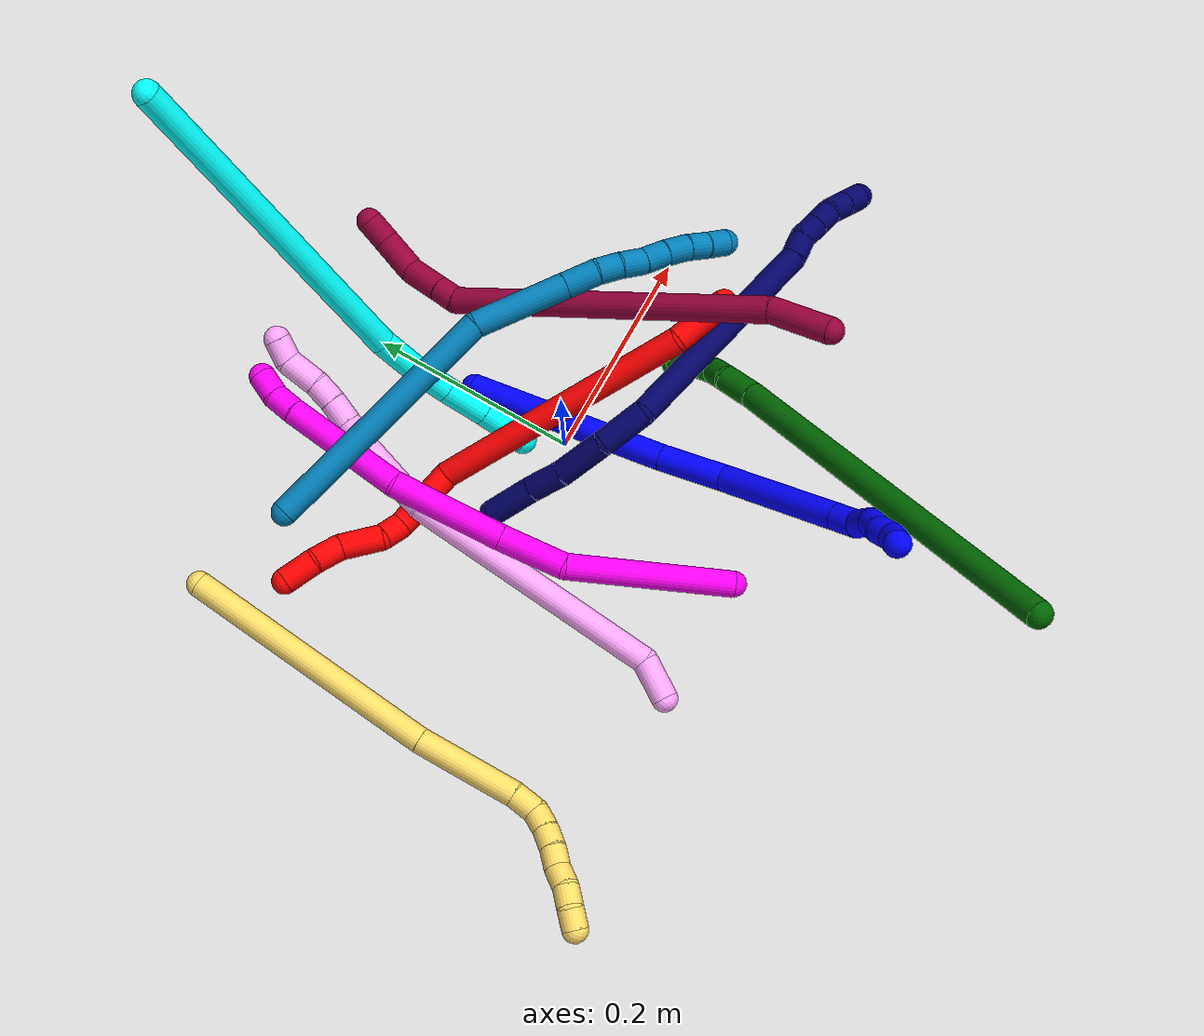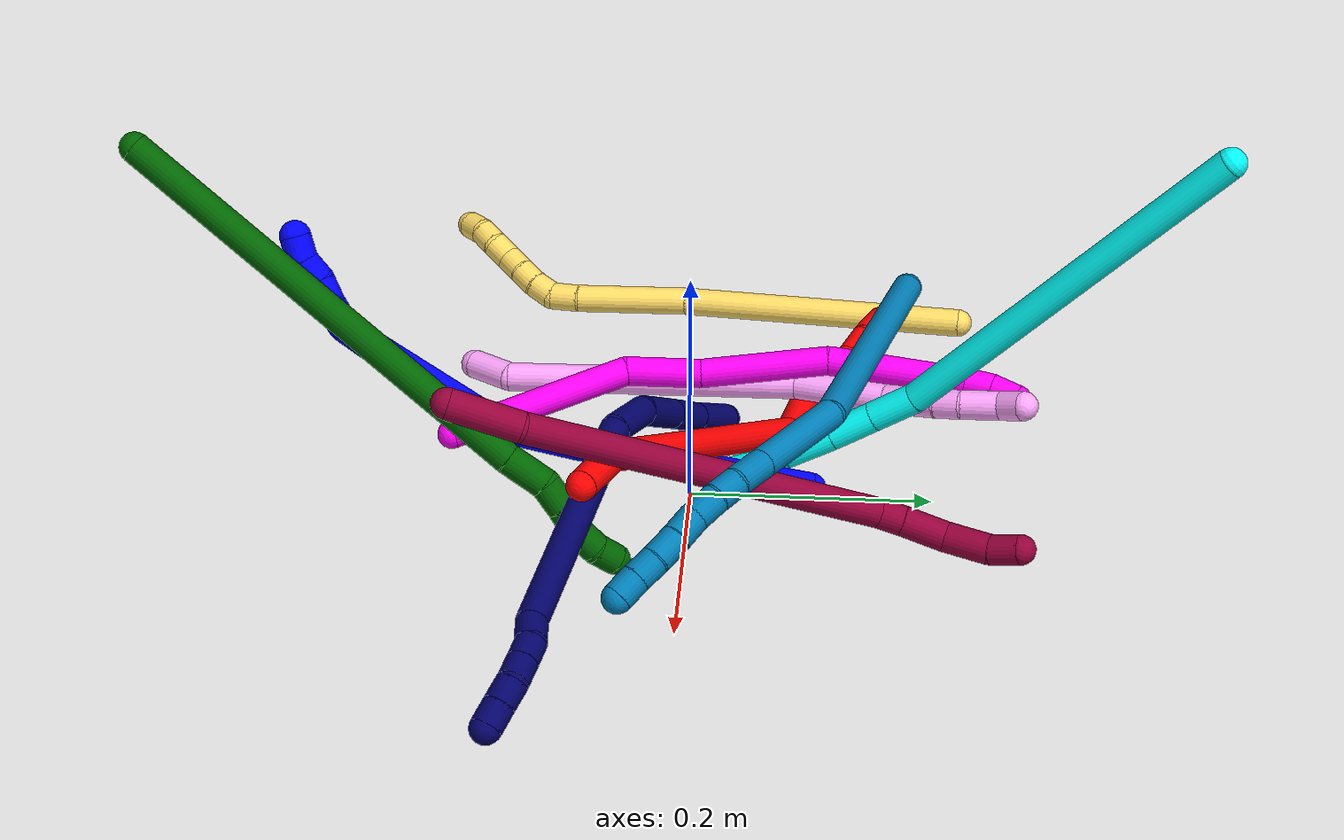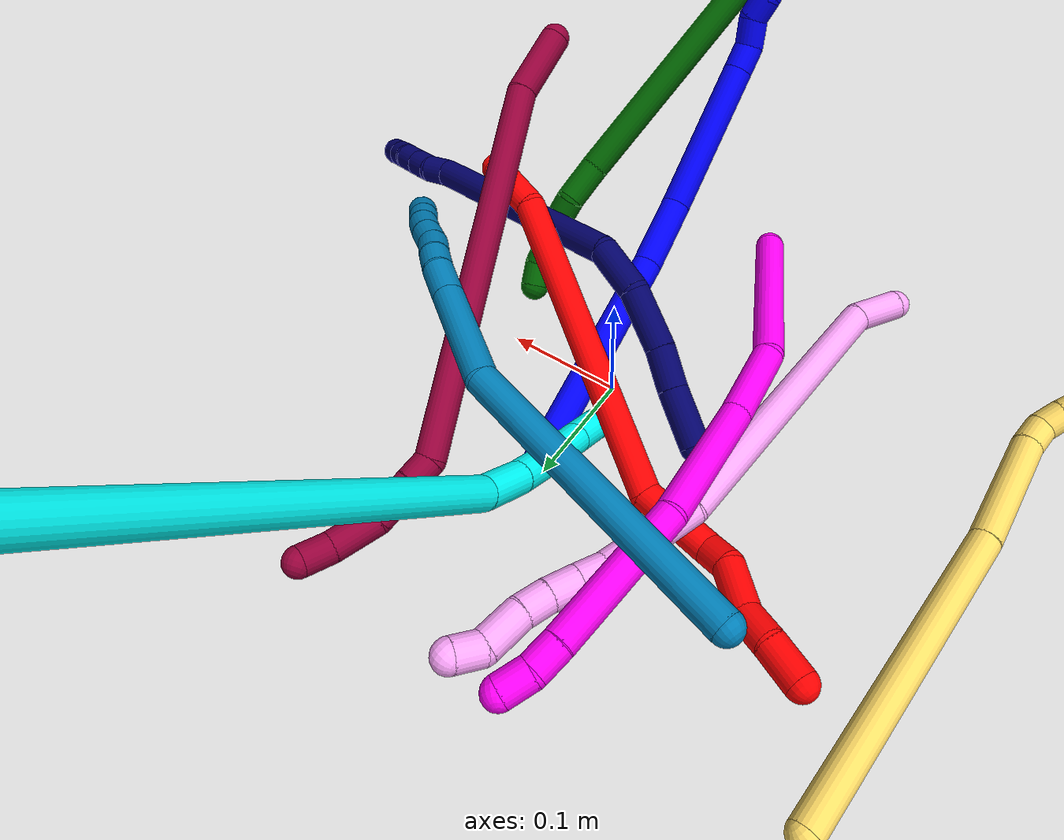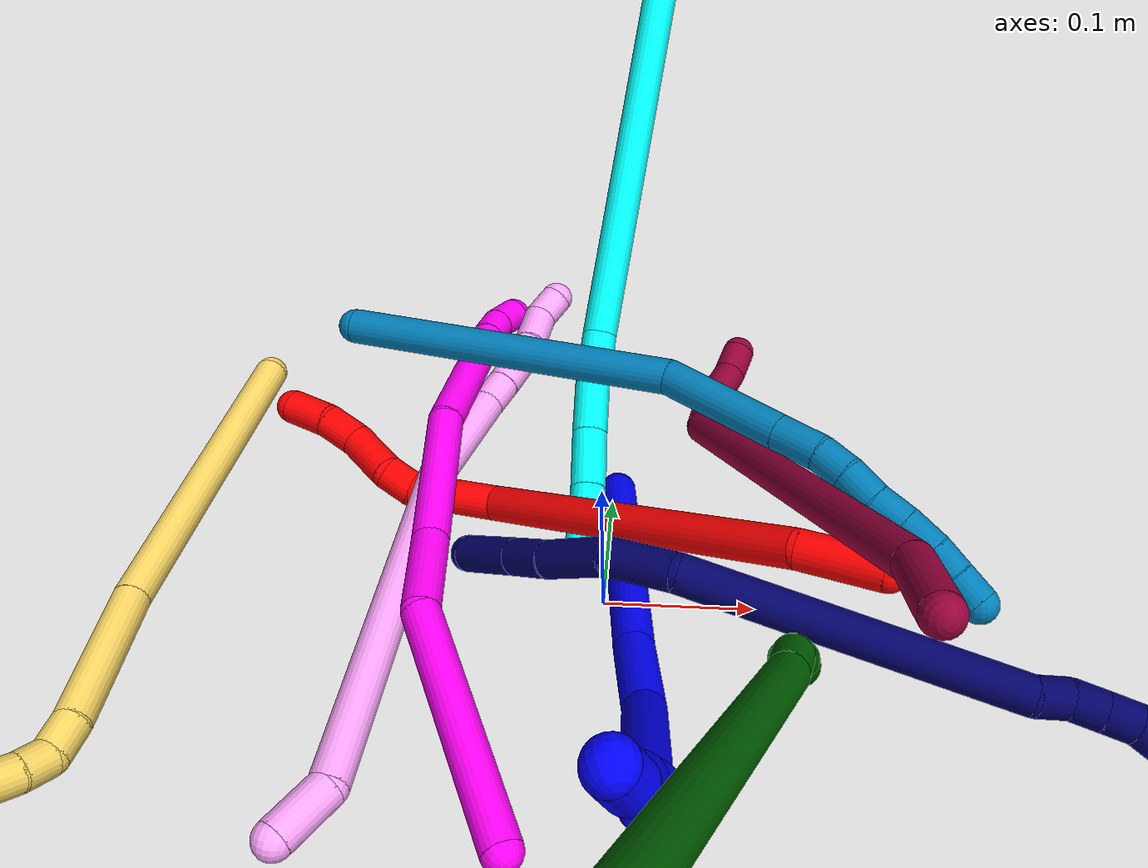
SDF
<sdf version="1.7">
 <world name="default">
  <plugin name="TubeGeneratorPlugin" filename="libtube_generator_plugin.so"/>
  <model name="photoneo_s_sensor">
   <static>1</static>
   <pose>0 0 2 1.57079 1.57079 3.14159</pose>
   <link name="link">
    <inertial><mass>0.1</mass></inertial>
    <sensor name="sensor" type="depth">
     <update_rate>30</update_rate>
     <camera>
      <horizontal_fov>1.22</horizontal_fov>
      <image><width>1920</width><height>1200</height><format>B8G8R8</format></image>
      <clip><near>0.1</near><far>2</far></clip>
      <depth_camera><output>points</output></depth_camera>
     </camera>
     <plugin name="camera_plugin" filename="libgazebo_ros_depth_camera.so">
      <baseline>0.2</baseline>
      <alwaysOn>1</alwaysOn>
      <updateRate>0.0</updateRate>
      <cameraName>camera_ir</cameraName>
      <imageTopicName>/camera/color/image_raw</imageTopicName>
      <cameraInfoTopicName>/camera/color/camera_info</cameraInfoTopicName>
      <depthImageTopicName>/camera/depth/image_raw</depthImageTopicName>
      <depthImageCameraInfoTopicName>/camera/depth/camera_info</depthImageCameraInfoTopicName>
      <pointCloudTopicName>/camera/depth/points</pointCloudTopicName>
      <frameName>fr_optical</frameName>
      <pointCloudCutoff>0.1</pointCloudCutoff>
      <pointCloudCutoffMax>2.0</pointCloudCutoffMax>
      <distortionK1>0</distortionK1>
      <distortionK2>0</distortionK2>
      <distortionK3>0</distortionK3>
      <distortionT1>0</distortionT1>
      <distortionT2>0</distortionT2>
      <CxPrime>0</CxPrime>
      <Cx>0</Cx>
      <Cy>0</Cy>
      <focalLength>0</focalLength>
      <hackBaseline>0</hackBaseline>
     </plugin>
    </sensor>
   </link>
  </model>
  <gravity>0 0 -9.8</gravity>
  <magnetic_field>6e-06 2.3e-05 -4.2e-05</magnetic_field>
  <atmosphere type="adiabatic"/>
  <physics name="default_physics" default="0" type="ode">
   <max_step_size>0.003</max_step_size>
   <real_time_factor>1</real_time_factor>
   <real_time_update_rate>1000</real_time_update_rate>
   <max_contacts>10000</max_contacts>
   <ode>
    <solver>
     <type>quick</type>
     <iters>100</iters>
     <sor>1.3</sor>
     <use_dynamic_moi_rescaling>0</use_dynamic_moi_rescaling>
    </solver>
    <constraints>
     <contact_max_correcting_vel>0</contact_max_correcting_vel>
     <contact_surface_layer>0.001</contact_surface_layer>
     <cfm>0</cfm>
     <erp>0.2</erp>
    </constraints>
   </ode>
  </physics>
  <scene><ambient>0.4 0.4 0.4 1</ambient><background>0.7 0.7 0.7 1</background><shadows>0</shadows></scene>
  <audio><device>default</device></audio>
  <spherical_coordinates>
   <surface_model>EARTH_WGS84</surface_model>
   <latitude_deg>0</latitude_deg>
   <longitude_deg>0</longitude_deg>
   <elevation>0</elevation>
   <heading_deg>0</heading_deg>
  </spherical_coordinates>
  <model name="bin">
   <static>1</static>
   <link name="bottom">
    <collision name="collision-bottom">
     <pose>0 0 -0.01 0 -0 0</pose>
     <geometry><box><size>0.8 0.6 0.02</size></box></geometry>
     <surface>
      <friction><ode><mu>100</mu><mu2>100</mu2></ode></friction>
      <contact><collide_bitmask>65535</collide_bitmask></contact>
     </surface>
    </collision>
   </link>
   <link name="west_wall">
    <collision name="collision-west_wall">
     <pose>-0.41 0 0.1 0 -0 0</pose>
     <geometry><box><size>0.02 0.6 0.2</size></box></geometry>
     <surface>
      <friction><ode><mu>100</mu><mu2>100</mu2></ode></friction>
      <contact><collide_bitmask>65535</collide_bitmask></contact>
     </surface>
    </collision>
   </link>
   <link name="east_wall">
    <collision name="collision-east_wall">
     <pose>0.41 0 0.1 0 -0 0</pose>
     <geometry><box><size>0.02 0.6 0.2</size></box></geometry>
     <surface>
      <friction><ode><mu>100</mu><mu2>100</mu2></ode></friction>
      <contact><collide_bitmask>65535</collide_bitmask></contact>
     </surface>
    </collision>
   </link>
   <link name="south_wall">
    <collision name="collision-south_wall">
     <pose>0 -0.31 0.1 0 -0 0</pose>
     <geometry><box><size>0.8 0.02 0.2</size></box></geometry>
     <surface>
      <friction><ode><mu>100</mu><mu2>100</mu2></ode></friction>
      <contact><collide_bitmask>65535</collide_bitmask></contact>
     </surface>
    </collision>
   </link>
   <link name="north_wall">
    <collision name="collision-north_wall">
     <pose>0 0.31 0.1 0 -0 0</pose>
     <geometry><box><size>0.8 0.02 0.2</size></box></geometry>
     <surface>
      <friction><ode><mu>100</mu><mu2>100</mu2></ode></friction>
      <contact><collide_bitmask>65535</collide_bitmask></contact>
     </surface>
    </collision>
   </link>
  </model>
  <model name="1">
   <static>0</static>
   <link name="1">
    <collision name="collision-cylinder-e_1_1_4">
     <pose>0.005605 -0.043584 0.088507 0.457573 0.056751 0.013219</pose>
     <geometry><cylinder><radius>0.0125</radius><length>0.197631</length></cylinder></geometry>
     <surface>
      <friction><ode><mu>1.16</mu><mu2>1.16</mu2><slip1>0</slip1><slip2>0</slip2></ode></friction>
      <contact><ode><kp>1e+06</kp><kd>1</kd><max_vel>0</max_vel><min_depth>0.001</min_depth></ode></contact>
     </surface>
    </collision>
    <visual name="visual-cylinder-e_1_1_4">
     <pose>0.005605 -0.043584 0.088507 0.457573 0.056751 0.013219</pose>
     <geometry><cylinder><radius>0.0125</radius><length>0.197631</length></cylinder></geometry>
     <material><ambient>0 0 1 1</ambient></material>
    </visual>
    <collision name="collision-cylinder-e_2_4_5">
     <pose>0.0116 -0.103086 0.204728 0.521403 0.012227 0.003262</pose>
     <geometry><cylinder><radius>0.0125</radius><length>0.063925</length></cylinder></geometry>
     <surface>
      <friction><ode><mu>1.16</mu><mu2>1.16</mu2><slip1>0</slip1><slip2>0</slip2></ode></friction>
      <contact><ode><kp>1e+06</kp><kd>1</kd><max_vel>0</max_vel><min_depth>0.001</min_depth></ode></contact>
     </surface>
    </collision>
    <visual name="visual-cylinder-e_2_4_5">
     <pose>0.0116 -0.103086 0.204728 0.521403 0.012227 0.003262</pose>
     <geometry><cylinder><radius>0.0125</radius><length>0.063925</length></cylinder></geometry>
     <material><ambient>0 0 1 1</ambient></material>
    </visual>
    <collision name="collision-cylinder-e_3_5_6">
     <pose>0.012405 -0.168196 0.274987 0.857707 0.006362 0.002909</pose>
     <geometry><cylinder><radius>0.0125</radius><length>0.130078</length></cylinder></geometry>
     <surface>
      <friction><ode><mu>1.16</mu><mu2>1.16</mu2><slip1>0</slip1><slip2>0</slip2></ode></friction>
      <contact><ode><kp>1e+06</kp><kd>1</kd><max_vel>0</max_vel><min_depth>0.001</min_depth></ode></contact>
     </surface>
    </collision>
    <visual name="visual-cylinder-e_3_5_6">
     <pose>0.012405 -0.168196 0.274987 0.857707 0.006362 0.002909</pose>
     <geometry><cylinder><radius>0.0125</radius><length>0.130078</length></cylinder></geometry>
     <material><ambient>0 0 1 1</ambient></material>
    </visual>
    <collision name="collision-cylinder-e_4_6_7">
     <pose>0.012909 -0.226732 0.324757 0.912668 0.007678 0.003769</pose>
     <geometry><cylinder><radius>0.0125</radius><length>0.023624</length></cylinder></geometry>
     <surface>
      <friction><ode><mu>1.16</mu><mu2>1.16</mu2><slip1>0</slip1><slip2>0</slip2></ode></friction>
      <contact><ode><kp>1e+06</kp><kd>1</kd><max_vel>0</max_vel><min_depth>0.001</min_depth></ode></contact>
     </surface>
    </collision>
    <visual name="visual-cylinder-e_4_6_7">
     <pose>0.012909 -0.226732 0.324757 0.912668 0.007678 0.003769</pose>
     <geometry><cylinder><radius>0.0125</radius><length>0.023624</length></cylinder></geometry>
     <material><ambient>0 0 1 1</ambient></material>
    </visual>
    <collision name="collision-cylinder-e_5_7_8">
     <pose>0.009827 -0.247631 0.334619 1.34636 -0.261558 -0.209011</pose>
     <geometry><cylinder><radius>0.0125</radius><length>0.024539</length></cylinder></geometry>
     <surface>
      <friction><ode><mu>1.16</mu><mu2>1.16</mu2><slip1>0</slip1><slip2>0</slip2></ode></friction>
      <contact><ode><kp>1e+06</kp><kd>1</kd><max_vel>0</max_vel><min_depth>0.001</min_depth></ode></contact>
     </surface>
    </collision>
    <visual name="visual-cylinder-e_5_7_8">
     <pose>0.009827 -0.247631 0.334619 1.34636 -0.261558 -0.209011</pose>
     <geometry><cylinder><radius>0.0125</radius><length>0.024539</length></cylinder></geometry>
     <material><ambient>0 0 1 1</ambient></material>
    </visual>
    <collision name="collision-cylinder-e_6_8_9">
     <pose>0.008468 -0.268985 0.338785 1.4161 0.18087 0.154962</pose>
     <geometry><cylinder><radius>0.0125</radius><length>0.020163</length></cylinder></geometry>
     <surface>
      <friction><ode><mu>1.16</mu><mu2>1.16</mu2><slip1>0</slip1><slip2>0</slip2></ode></friction>
      <contact><ode><kp>1e+06</kp><kd>1</kd><max_vel>0</max_vel><min_depth>0.001</min_depth></ode></contact>
     </surface>
    </collision>
    <visual name="visual-cylinder-e_6_8_9">
     <pose>0.008468 -0.268985 0.338785 1.4161 0.18087 0.154962</pose>
     <geometry><cylinder><radius>0.0125</radius><length>0.020163</length></cylinder></geometry>
     <material><ambient>0 0 1 1</ambient></material>
    </visual>
    <collision name="collision-cylinder-e_7_9_10">
     <pose>0.011176 -0.287893 0.344382 1.15071 0.089415 0.058012</pose>
     <geometry><cylinder><radius>0.0125</radius><length>0.020035</length></cylinder></geometry>
     <surface>
      <friction><ode><mu>1.16</mu><mu2>1.16</mu2><slip1>0</slip1><slip2>0</slip2></ode></friction>
      <contact><ode><kp>1e+06</kp><kd>1</kd><max_vel>0</max_vel><min_depth>0.001</min_depth></ode></contact>
     </surface>
    </collision>
    <visual name="visual-cylinder-e_7_9_10">
     <pose>0.011176 -0.287893 0.344382 1.15071 0.089415 0.058012</pose>
     <geometry><cylinder><radius>0.0125</radius><length>0.020035</length></cylinder></geometry>
     <material><ambient>0 0 1 1</ambient></material>
    </visual>
    <collision name="collision-cylinder-e_8_10_2">
     <pose>0.013759 -0.306862 0.34852 1.56382 0.169615 0.168442</pose>
     <geometry><cylinder><radius>0.0125</radius><length>0.020006</length></cylinder></geometry>
     <surface>
      <friction><ode><mu>1.16</mu><mu2>1.16</mu2><slip1>0</slip1><slip2>0</slip2></ode></friction>
      <contact><ode><kp>1e+06</kp><kd>1</kd><max_vel>0</max_vel><min_depth>0.001</min_depth></ode></contact>
     </surface>
    </collision>
    <visual name="visual-cylinder-e_8_10_2">
     <pose>0.013759 -0.306862 0.34852 1.56382 0.169615 0.168442</pose>
     <geometry><cylinder><radius>0.0125</radius><length>0.020006</length></cylinder></geometry>
     <material><ambient>0 0 1 1</ambient></material>
    </visual>
    <collision name="collision-sphere-2">
     <pose>0.015448 -0.316722 0.348589 0 -0 0</pose>
     <geometry><sphere><radius>0.0125</radius></sphere></geometry>
     <surface>
      <friction><ode><mu>1.16</mu><mu2>1.16</mu2><slip1>0</slip1><slip2>0</slip2></ode></friction>
      <contact><ode><kp>1e+06</kp><kd>1</kd><max_vel>0</max_vel><min_depth>0.001</min_depth></ode></contact>
     </surface>
    </collision>
    <visual name="visual-sphere-2">
     <pose>0.015448 -0.316722 0.348589 0 -0 0</pose>
     <geometry><sphere><radius>0.0125</radius></sphere></geometry>
     <material><ambient>0 0 1 1</ambient></material>
    </visual>
    <collision name="collision-sphere-10">
     <pose>0.012071 -0.297003 0.348452 0 -0 0</pose>
     <geometry><sphere><radius>0.0125</radius></sphere></geometry>
     <surface>
      <friction><ode><mu>1.16</mu><mu2>1.16</mu2><slip1>0</slip1><slip2>0</slip2></ode></friction>
      <contact><ode><kp>1e+06</kp><kd>1</kd><max_vel>0</max_vel><min_depth>0.001</min_depth></ode></contact>
     </surface>
    </collision>
    <visual name="visual-sphere-10">
     <pose>0.012071 -0.297003 0.348452 0 -0 0</pose>
     <geometry><sphere><radius>0.0125</radius></sphere></geometry>
     <material><ambient>0 0 1 1</ambient></material>
    </visual>
    <collision name="collision-sphere-9">
     <pose>0.010282 -0.278783 0.340313 0 -0 0</pose>
     <geometry><sphere><radius>0.0125</radius></sphere></geometry>
     <surface>
      <friction><ode><mu>1.16</mu><mu2>1.16</mu2><slip1>0</slip1><slip2>0</slip2></ode></friction>
      <contact><ode><kp>1e+06</kp><kd>1</kd><max_vel>0</max_vel><min_depth>0.001</min_depth></ode></contact>
     </surface>
    </collision>
    <visual name="visual-sphere-9">
     <pose>0.010282 -0.278783 0.340313 0 -0 0</pose>
     <geometry><sphere><radius>0.0125</radius></sphere></geometry>
     <material><ambient>0 0 1 1</ambient></material>
    </visual>
    <collision name="collision-sphere-4">
     <pose>0.01121 -0.087167 0.177015 0 -0 0</pose>
     <geometry><sphere><radius>0.0125</radius></sphere></geometry>
     <surface>
      <friction><ode><mu>1.16</mu><mu2>1.16</mu2><slip1>0</slip1><slip2>0</slip2></ode></friction>
      <contact><ode><kp>1e+06</kp><kd>1</kd><max_vel>0</max_vel><min_depth>0.001</min_depth></ode></contact>
     </surface>
    </collision>
    <visual name="visual-sphere-4">
     <pose>0.01121 -0.087167 0.177015 0 -0 0</pose>
     <geometry><sphere><radius>0.0125</radius></sphere></geometry>
     <material><ambient>0 0 1 1</ambient></material>
    </visual>
    <collision name="collision-sphere-1">
     <geometry><sphere><radius>0.0125</radius></sphere></geometry>
     <surface>
      <friction><ode><mu>1.16</mu><mu2>1.16</mu2><slip1>0</slip1><slip2>0</slip2></ode></friction>
      <contact><ode><kp>1e+06</kp><kd>1</kd><max_vel>0</max_vel><min_depth>0.001</min_depth></ode></contact>
     </surface>
    </collision>
    <visual name="visual-sphere-1">
     <geometry><sphere><radius>0.0125</radius></sphere></geometry>
     <material><ambient>0 0 1 1</ambient></material>
    </visual>
    <collision name="collision-sphere-8">
     <pose>0.006655 -0.259186 0.337257 0 -0 0</pose>
     <geometry><sphere><radius>0.0125</radius></sphere></geometry>
     <surface>
      <friction><ode><mu>1.16</mu><mu2>1.16</mu2><slip1>0</slip1><slip2>0</slip2></ode></friction>
      <contact><ode><kp>1e+06</kp><kd>1</kd><max_vel>0</max_vel><min_depth>0.001</min_depth></ode></contact>
     </surface>
    </collision>
    <visual name="visual-sphere-8">
     <pose>0.006655 -0.259186 0.337257 0 -0 0</pose>
     <geometry><sphere><radius>0.0125</radius></sphere></geometry>
     <material><ambient>0 0 1 1</ambient></material>
    </visual>
    <collision name="collision-sphere-5">
     <pose>0.011991 -0.119005 0.232441 0 -0 0</pose>
     <geometry><sphere><radius>0.0125</radius></sphere></geometry>
     <surface>
      <friction><ode><mu>1.16</mu><mu2>1.16</mu2><slip1>0</slip1><slip2>0</slip2></ode></friction>
      <contact><ode><kp>1e+06</kp><kd>1</kd><max_vel>0</max_vel><min_depth>0.001</min_depth></ode></contact>
     </surface>
    </collision>
    <visual name="visual-sphere-5">
     <pose>0.011991 -0.119005 0.232441 0 -0 0</pose>
     <geometry><sphere><radius>0.0125</radius></sphere></geometry>
     <material><ambient>0 0 1 1</ambient></material>
    </visual>
    <collision name="collision-sphere-6">
     <pose>0.012819 -0.217387 0.317533 0 -0 0</pose>
     <geometry><sphere><radius>0.0125</radius></sphere></geometry>
     <surface>
      <friction><ode><mu>1.16</mu><mu2>1.16</mu2><slip1>0</slip1><slip2>0</slip2></ode></friction>
      <contact><ode><kp>1e+06</kp><kd>1</kd><max_vel>0</max_vel><min_depth>0.001</min_depth></ode></contact>
     </surface>
    </collision>
    <visual name="visual-sphere-6">
     <pose>0.012819 -0.217387 0.317533 0 -0 0</pose>
     <geometry><sphere><radius>0.0125</radius></sphere></geometry>
     <material><ambient>0 0 1 1</ambient></material>
    </visual>
    <collision name="collision-sphere-7">
     <pose>0.013 -0.236077 0.331982 0 -0 0</pose>
     <geometry><sphere><radius>0.0125</radius></sphere></geometry>
     <surface>
      <friction><ode><mu>1.16</mu><mu2>1.16</mu2><slip1>0</slip1><slip2>0</slip2></ode></friction>
      <contact><ode><kp>1e+06</kp><kd>1</kd><max_vel>0</max_vel><min_depth>0.001</min_depth></ode></contact>
     </surface>
    </collision>
    <visual name="visual-sphere-7">
     <pose>0.013 -0.236077 0.331982 0 -0 0</pose>
     <geometry><sphere><radius>0.0125</radius></sphere></geometry>
     <material><ambient>0 0 1 1</ambient></material>
    </visual>
    <inertial>
     <pose>0.009358 -0.13169 0.20587 0 -0 0</pose>
     <mass>0.5</mass>
     <inertia>
      <ixx>0.000882</ixx>
      <ixy>0</ixy>
      <ixz>0</ixz>
      <iyy>0.000716</iyy>
      <iyz>0</iyz>
      <izz>0.000438</izz>
     </inertia>
    </inertial>
   </link>
   <pose>0.004101 0.100392 0.012304 -1.7726 0.231234 -2.91738</pose>
  </model>
  <model name="2">
   <static>0</static>
   <link name="2">
    <collision name="collision-cylinder-e_1_1_4">
     <pose>-0.001919 -0.000688 0.026696 0.025771 -0.071733 -0.000925</pose>
     <geometry><cylinder><radius>0.0125</radius><length>0.053548</length></cylinder></geometry>
     <surface>
      <friction><ode><mu>1.16</mu><mu2>1.16</mu2><slip1>0</slip1><slip2>0</slip2></ode></friction>
      <contact><ode><kp>1e+06</kp><kd>1</kd><max_vel>0</max_vel><min_depth>0.001</min_depth></ode></contact>
     </surface>
    </collision>
    <visual name="visual-cylinder-e_1_1_4">
     <pose>-0.001919 -0.000688 0.026696 0.025771 -0.071733 -0.000925</pose>
     <geometry><cylinder><radius>0.0125</radius><length>0.053548</length></cylinder></geometry>
     <material><ambient>1 0 0 1</ambient></material>
    </visual>
    <collision name="collision-cylinder-e_2_4_5">
     <pose>-0.028869 0.039243 0.173476 -0.326175 -0.194951 0.032178</pose>
     <geometry><cylinder><radius>0.0125</radius><length>0.258431</length></cylinder></geometry>
     <surface>
      <friction><ode><mu>1.16</mu><mu2>1.16</mu2><slip1>0</slip1><slip2>0</slip2></ode></friction>
      <contact><ode><kp>1e+06</kp><kd>1</kd><max_vel>0</max_vel><min_depth>0.001</min_depth></ode></contact>
     </surface>
    </collision>
    <visual name="visual-cylinder-e_2_4_5">
     <pose>-0.028869 0.039243 0.173476 -0.326175 -0.194951 0.032178</pose>
     <geometry><cylinder><radius>0.0125</radius><length>0.258431</length></cylinder></geometry>
     <material><ambient>1 0 0 1</ambient></material>
    </visual>
    <collision name="collision-cylinder-e_3_5_6">
     <pose>-0.058161 0.073931 0.324587 0.18889 -0.134073 -0.012719</pose>
     <geometry><cylinder><radius>0.0125</radius><length>0.063749</length></cylinder></geometry>
     <surface>
      <friction><ode><mu>1.16</mu><mu2>1.16</mu2><slip1>0</slip1><slip2>0</slip2></ode></friction>
      <contact><ode><kp>1e+06</kp><kd>1</kd><max_vel>0</max_vel><min_depth>0.001</min_depth></ode></contact>
     </surface>
    </collision>
    <visual name="visual-cylinder-e_3_5_6">
     <pose>-0.058161 0.073931 0.324587 0.18889 -0.134073 -0.012719</pose>
     <geometry><cylinder><radius>0.0125</radius><length>0.063749</length></cylinder></geometry>
     <material><ambient>1 0 0 1</ambient></material>
    </visual>
    <collision name="collision-cylinder-e_4_6_7">
     <pose>-0.058785 0.064869 0.366249 0.286298 0.317004 0.04607</pose>
     <geometry><cylinder><radius>0.0125</radius><length>0.023337</length></cylinder></geometry>
     <surface>
      <friction><ode><mu>1.16</mu><mu2>1.16</mu2><slip1>0</slip1><slip2>0</slip2></ode></friction>
      <contact><ode><kp>1e+06</kp><kd>1</kd><max_vel>0</max_vel><min_depth>0.001</min_depth></ode></contact>
     </surface>
    </collision>
    <visual name="visual-cylinder-e_4_6_7">
     <pose>-0.058785 0.064869 0.366249 0.286298 0.317004 0.04607</pose>
     <geometry><cylinder><radius>0.0125</radius><length>0.023337</length></cylinder></geometry>
     <material><ambient>1 0 0 1</ambient></material>
    </visual>
    <collision name="collision-cylinder-e_5_7_8">
     <pose>-0.048575 0.065769 0.395602 -0.212131 0.330642 -0.035522</pose>
     <geometry><cylinder><radius>0.0125</radius><length>0.040486</length></cylinder></geometry>
     <surface>
      <friction><ode><mu>1.16</mu><mu2>1.16</mu2><slip1>0</slip1><slip2>0</slip2></ode></friction>
      <contact><ode><kp>1e+06</kp><kd>1</kd><max_vel>0</max_vel><min_depth>0.001</min_depth></ode></contact>
     </surface>
    </collision>
    <visual name="visual-cylinder-e_5_7_8">
     <pose>-0.048575 0.065769 0.395602 -0.212131 0.330642 -0.035522</pose>
     <geometry><cylinder><radius>0.0125</radius><length>0.040486</length></cylinder></geometry>
     <material><ambient>1 0 0 1</ambient></material>
    </visual>
    <collision name="collision-cylinder-e_6_8_9">
     <pose>-0.038167 0.067947 0.427633 0.138282 0.278048 0.01938</pose>
     <geometry><cylinder><radius>0.0125</radius><length>0.027957</length></cylinder></geometry>
     <surface>
      <friction><ode><mu>1.16</mu><mu2>1.16</mu2><slip1>0</slip1><slip2>0</slip2></ode></friction>
      <contact><ode><kp>1e+06</kp><kd>1</kd><max_vel>0</max_vel><min_depth>0.001</min_depth></ode></contact>
     </surface>
    </collision>
    <visual name="visual-cylinder-e_6_8_9">
     <pose>-0.038167 0.067947 0.427633 0.138282 0.278048 0.01938</pose>
     <geometry><cylinder><radius>0.0125</radius><length>0.027957</length></cylinder></geometry>
     <material><ambient>1 0 0 1</ambient></material>
    </visual>
    <collision name="collision-cylinder-e_7_9_2">
     <pose>-0.033447 0.065468 0.457156 0.038614 0.054362 0.00105</pose>
     <geometry><cylinder><radius>0.0125</radius><length>0.032493</length></cylinder></geometry>
     <surface>
      <friction><ode><mu>1.16</mu><mu2>1.16</mu2><slip1>0</slip1><slip2>0</slip2></ode></friction>
      <contact><ode><kp>1e+06</kp><kd>1</kd><max_vel>0</max_vel><min_depth>0.001</min_depth></ode></contact>
     </surface>
    </collision>
    <visual name="visual-cylinder-e_7_9_2">
     <pose>-0.033447 0.065468 0.457156 0.038614 0.054362 0.00105</pose>
     <geometry><cylinder><radius>0.0125</radius><length>0.032493</length></cylinder></geometry>
     <material><ambient>1 0 0 1</ambient></material>
    </visual>
    <collision name="collision-sphere-2">
     <pose>-0.032565 0.064842 0.473366 0 -0 0</pose>
     <geometry><sphere><radius>0.0125</radius></sphere></geometry>
     <surface>
      <friction><ode><mu>1.16</mu><mu2>1.16</mu2><slip1>0</slip1><slip2>0</slip2></ode></friction>
      <contact><ode><kp>1e+06</kp><kd>1</kd><max_vel>0</max_vel><min_depth>0.001</min_depth></ode></contact>
     </surface>
    </collision>
    <visual name="visual-sphere-2">
     <pose>-0.032565 0.064842 0.473366 0 -0 0</pose>
     <geometry><sphere><radius>0.0125</radius></sphere></geometry>
     <material><ambient>1 0 0 1</ambient></material>
    </visual>
    <collision name="collision-sphere-9">
     <pose>-0.03433 0.066094 0.440946 0 -0 0</pose>
     <geometry><sphere><radius>0.0125</radius></sphere></geometry>
     <surface>
      <friction><ode><mu>1.16</mu><mu2>1.16</mu2><slip1>0</slip1><slip2>0</slip2></ode></friction>
      <contact><ode><kp>1e+06</kp><kd>1</kd><max_vel>0</max_vel><min_depth>0.001</min_depth></ode></contact>
     </surface>
    </collision>
    <visual name="visual-sphere-9">
     <pose>-0.03433 0.066094 0.440946 0 -0 0</pose>
     <geometry><sphere><radius>0.0125</radius></sphere></geometry>
     <material><ambient>1 0 0 1</ambient></material>
    </visual>
    <collision name="collision-sphere-4">
     <pose>-0.003838 -0.001376 0.053392 0 -0 0</pose>
     <geometry><sphere><radius>0.0125</radius></sphere></geometry>
     <surface>
      <friction><ode><mu>1.16</mu><mu2>1.16</mu2><slip1>0</slip1><slip2>0</slip2></ode></friction>
      <contact><ode><kp>1e+06</kp><kd>1</kd><max_vel>0</max_vel><min_depth>0.001</min_depth></ode></contact>
     </surface>
    </collision>
    <visual name="visual-sphere-4">
     <pose>-0.003838 -0.001376 0.053392 0 -0 0</pose>
     <geometry><sphere><radius>0.0125</radius></sphere></geometry>
     <material><ambient>1 0 0 1</ambient></material>
    </visual>
    <collision name="collision-sphere-1">
     <geometry><sphere><radius>0.0125</radius></sphere></geometry>
     <surface>
      <friction><ode><mu>1.16</mu><mu2>1.16</mu2><slip1>0</slip1><slip2>0</slip2></ode></friction>
      <contact><ode><kp>1e+06</kp><kd>1</kd><max_vel>0</max_vel><min_depth>0.001</min_depth></ode></contact>
     </surface>
    </collision>
    <visual name="visual-sphere-1">
     <geometry><sphere><radius>0.0125</radius></sphere></geometry>
     <material><ambient>1 0 0 1</ambient></material>
    </visual>
    <collision name="collision-sphere-8">
     <pose>-0.042004 0.0698 0.41432 0 -0 0</pose>
     <geometry><sphere><radius>0.0125</radius></sphere></geometry>
     <surface>
      <friction><ode><mu>1.16</mu><mu2>1.16</mu2><slip1>0</slip1><slip2>0</slip2></ode></friction>
      <contact><ode><kp>1e+06</kp><kd>1</kd><max_vel>0</max_vel><min_depth>0.001</min_depth></ode></contact>
     </surface>
    </collision>
    <visual name="visual-sphere-8">
     <pose>-0.042004 0.0698 0.41432 0 -0 0</pose>
     <geometry><sphere><radius>0.0125</radius></sphere></geometry>
     <material><ambient>1 0 0 1</ambient></material>
    </visual>
    <collision name="collision-sphere-5">
     <pose>-0.053901 0.079862 0.293561 0 -0 0</pose>
     <geometry><sphere><radius>0.0125</radius></sphere></geometry>
     <surface>
      <friction><ode><mu>1.16</mu><mu2>1.16</mu2><slip1>0</slip1><slip2>0</slip2></ode></friction>
      <contact><ode><kp>1e+06</kp><kd>1</kd><max_vel>0</max_vel><min_depth>0.001</min_depth></ode></contact>
     </surface>
    </collision>
    <visual name="visual-sphere-5">
     <pose>-0.053901 0.079862 0.293561 0 -0 0</pose>
     <geometry><sphere><radius>0.0125</radius></sphere></geometry>
     <material><ambient>1 0 0 1</ambient></material>
    </visual>
    <collision name="collision-sphere-6">
     <pose>-0.062422 0.068 0.355613 0 -0 0</pose>
     <geometry><sphere><radius>0.0125</radius></sphere></geometry>
     <surface>
      <friction><ode><mu>1.16</mu><mu2>1.16</mu2><slip1>0</slip1><slip2>0</slip2></ode></friction>
      <contact><ode><kp>1e+06</kp><kd>1</kd><max_vel>0</max_vel><min_depth>0.001</min_depth></ode></contact>
     </surface>
    </collision>
    <visual name="visual-sphere-6">
     <pose>-0.062422 0.068 0.355613 0 -0 0</pose>
     <geometry><sphere><radius>0.0125</radius></sphere></geometry>
     <material><ambient>1 0 0 1</ambient></material>
    </visual>
    <collision name="collision-sphere-7">
     <pose>-0.055147 0.061737 0.376885 0 -0 0</pose>
     <geometry><sphere><radius>0.0125</radius></sphere></geometry>
     <surface>
      <friction><ode><mu>1.16</mu><mu2>1.16</mu2><slip1>0</slip1><slip2>0</slip2></ode></friction>
      <contact><ode><kp>1e+06</kp><kd>1</kd><max_vel>0</max_vel><min_depth>0.001</min_depth></ode></contact>
     </surface>
    </collision>
    <visual name="visual-sphere-7">
     <pose>-0.055147 0.061737 0.376885 0 -0 0</pose>
     <geometry><sphere><radius>0.0125</radius></sphere></geometry>
     <material><ambient>1 0 0 1</ambient></material>
    </visual>
    <inertial>
     <pose>-0.033527 0.046042 0.236652 0 -0 0</pose>
     <mass>0.5</mass>
     <inertia>
      <ixx>0.001517</ixx>
      <ixy>0</ixy>
      <ixz>0</ixz>
      <iyy>0.001479</iyy>
      <iyz>0</iyz>
      <izz>-0.000133</izz>
     </inertia>
    </inertial>
   </link>
   <pose>0.167825 -0.072355 0.111537 -1.61716 -0.945583 1.17309</pose>
  </model>
  <model name="3">
   <static>0</static>
   <link name="3">
    <collision name="collision-cylinder-e_1_1_4">
     <pose>-0.015976 0.021845 -0.163456 -3.00874 -0.096577 1.25649</pose>
     <geometry><cylinder><radius>0.0125</radius><length>0.331363</length></cylinder></geometry>
     <surface>
      <friction><ode><mu>1.16</mu><mu2>1.16</mu2><slip1>0</slip1><slip2>0</slip2></ode></friction>
      <contact><ode><kp>1e+06</kp><kd>1</kd><max_vel>0</max_vel><min_depth>0.001</min_depth></ode></contact>
     </surface>
    </collision>
    <visual name="visual-cylinder-e_1_1_4">
     <pose>-0.015976 0.021845 -0.163456 -3.00874 -0.096577 1.25649</pose>
     <geometry><cylinder><radius>0.0125</radius><length>0.331363</length></cylinder></geometry>
     <material><ambient>0.003922 1 0.996078 1</ambient></material>
    </visual>
    <collision name="collision-cylinder-e_2_4_5">
     <pose>-0.03573 0.041553 -0.346114 3.0308 -0.19308 -2.10149</pose>
     <geometry><cylinder><radius>0.0125</radius><length>0.039371</length></cylinder></geometry>
     <surface>
      <friction><ode><mu>1.16</mu><mu2>1.16</mu2><slip1>0</slip1><slip2>0</slip2></ode></friction>
      <contact><ode><kp>1e+06</kp><kd>1</kd><max_vel>0</max_vel><min_depth>0.001</min_depth></ode></contact>
     </surface>
    </collision>
    <visual name="visual-cylinder-e_2_4_5">
     <pose>-0.03573 0.041553 -0.346114 3.0308 -0.19308 -2.10149</pose>
     <geometry><cylinder><radius>0.0125</radius><length>0.039371</length></cylinder></geometry>
     <material><ambient>0.003922 1 0.996078 1</ambient></material>
    </visual>
    <collision name="collision-cylinder-e_3_5_6">
     <pose>-0.042375 0.035802 -0.384014 2.9506 -0.149483 -1.32702</pose>
     <geometry><cylinder><radius>0.0125</radius><length>0.03852</length></cylinder></geometry>
     <surface>
      <friction><ode><mu>1.16</mu><mu2>1.16</mu2><slip1>0</slip1><slip2>0</slip2></ode></friction>
      <contact><ode><kp>1e+06</kp><kd>1</kd><max_vel>0</max_vel><min_depth>0.001</min_depth></ode></contact>
     </surface>
    </collision>
    <visual name="visual-cylinder-e_3_5_6">
     <pose>-0.042375 0.035802 -0.384014 2.9506 -0.149483 -1.32702</pose>
     <geometry><cylinder><radius>0.0125</radius><length>0.03852</length></cylinder></geometry>
     <material><ambient>0.003922 1 0.996078 1</ambient></material>
    </visual>
    <collision name="collision-cylinder-e_4_6_7">
     <pose>-0.048609 0.02668 -0.422986 2.87639 -0.158851 -1.07601</pose>
     <geometry><cylinder><radius>0.0125</radius><length>0.04255</length></cylinder></geometry>
     <surface>
      <friction><ode><mu>1.16</mu><mu2>1.16</mu2><slip1>0</slip1><slip2>0</slip2></ode></friction>
      <contact><ode><kp>1e+06</kp><kd>1</kd><max_vel>0</max_vel><min_depth>0.001</min_depth></ode></contact>
     </surface>
    </collision>
    <visual name="visual-cylinder-e_4_6_7">
     <pose>-0.048609 0.02668 -0.422986 2.87639 -0.158851 -1.07601</pose>
     <geometry><cylinder><radius>0.0125</radius><length>0.04255</length></cylinder></geometry>
     <material><ambient>0.003922 1 0.996078 1</ambient></material>
    </visual>
    <collision name="collision-cylinder-e_5_7_8">
     <pose>-0.054462 0.017961 -0.456064 2.89577 -0.186251 -1.29469</pose>
     <geometry><cylinder><radius>0.0125</radius><length>0.02687</length></cylinder></geometry>
     <surface>
      <friction><ode><mu>1.16</mu><mu2>1.16</mu2><slip1>0</slip1><slip2>0</slip2></ode></friction>
      <contact><ode><kp>1e+06</kp><kd>1</kd><max_vel>0</max_vel><min_depth>0.001</min_depth></ode></contact>
     </surface>
    </collision>
    <visual name="visual-cylinder-e_5_7_8">
     <pose>-0.054462 0.017961 -0.456064 2.89577 -0.186251 -1.29469</pose>
     <geometry><cylinder><radius>0.0125</radius><length>0.02687</length></cylinder></geometry>
     <material><ambient>0.003922 1 0.996078 1</ambient></material>
    </visual>
    <collision name="collision-cylinder-e_6_8_2">
     <pose>-0.059944 0.01252 -0.478858 2.92207 -0.284609 -1.83028</pose>
     <geometry><cylinder><radius>0.0125</radius><length>0.021326</length></cylinder></geometry>
     <surface>
      <friction><ode><mu>1.16</mu><mu2>1.16</mu2><slip1>0</slip1><slip2>0</slip2></ode></friction>
      <contact><ode><kp>1e+06</kp><kd>1</kd><max_vel>0</max_vel><min_depth>0.001</min_depth></ode></contact>
     </surface>
    </collision>
    <visual name="visual-cylinder-e_6_8_2">
     <pose>-0.059944 0.01252 -0.478858 2.92207 -0.284609 -1.83028</pose>
     <geometry><cylinder><radius>0.0125</radius><length>0.021326</length></cylinder></geometry>
     <material><ambient>0.003922 1 0.996078 1</ambient></material>
    </visual>
    <collision name="collision-sphere-2">
     <pose>-0.062938 0.010291 -0.488847 0 -0 0</pose>
     <geometry><sphere><radius>0.0125</radius></sphere></geometry>
     <surface>
      <friction><ode><mu>1.16</mu><mu2>1.16</mu2><slip1>0</slip1><slip2>0</slip2></ode></friction>
      <contact><ode><kp>1e+06</kp><kd>1</kd><max_vel>0</max_vel><min_depth>0.001</min_depth></ode></contact>
     </surface>
    </collision>
    <visual name="visual-sphere-2">
     <pose>-0.062938 0.010291 -0.488847 0 -0 0</pose>
     <geometry><sphere><radius>0.0125</radius></sphere></geometry>
     <material><ambient>0.003922 1 0.996078 1</ambient></material>
    </visual>
    <collision name="collision-sphere-4">
     <pose>-0.031952 0.043689 -0.326913 0 -0 0</pose>
     <geometry><sphere><radius>0.0125</radius></sphere></geometry>
     <surface>
      <friction><ode><mu>1.16</mu><mu2>1.16</mu2><slip1>0</slip1><slip2>0</slip2></ode></friction>
      <contact><ode><kp>1e+06</kp><kd>1</kd><max_vel>0</max_vel><min_depth>0.001</min_depth></ode></contact>
     </surface>
    </collision>
    <visual name="visual-sphere-4">
     <pose>-0.031952 0.043689 -0.326913 0 -0 0</pose>
     <geometry><sphere><radius>0.0125</radius></sphere></geometry>
     <material><ambient>0.003922 1 0.996078 1</ambient></material>
    </visual>
    <collision name="collision-sphere-1">
     <geometry><sphere><radius>0.0125</radius></sphere></geometry>
     <surface>
      <friction><ode><mu>1.16</mu><mu2>1.16</mu2><slip1>0</slip1><slip2>0</slip2></ode></friction>
      <contact><ode><kp>1e+06</kp><kd>1</kd><max_vel>0</max_vel><min_depth>0.001</min_depth></ode></contact>
     </surface>
    </collision>
    <visual name="visual-sphere-1">
     <geometry><sphere><radius>0.0125</radius></sphere></geometry>
     <material><ambient>0.003922 1 0.996078 1</ambient></material>
    </visual>
    <collision name="collision-sphere-8">
     <pose>-0.05695 0.014748 -0.46887 0 -0 0</pose>
     <geometry><sphere><radius>0.0125</radius></sphere></geometry>
     <surface>
      <friction><ode><mu>1.16</mu><mu2>1.16</mu2><slip1>0</slip1><slip2>0</slip2></ode></friction>
      <contact><ode><kp>1e+06</kp><kd>1</kd><max_vel>0</max_vel><min_depth>0.001</min_depth></ode></contact>
     </surface>
    </collision>
    <visual name="visual-sphere-8">
     <pose>-0.05695 0.014748 -0.46887 0 -0 0</pose>
     <geometry><sphere><radius>0.0125</radius></sphere></geometry>
     <material><ambient>0.003922 1 0.996078 1</ambient></material>
    </visual>
    <collision name="collision-sphere-5">
     <pose>-0.039507 0.039417 -0.365316 0 -0 0</pose>
     <geometry><sphere><radius>0.0125</radius></sphere></geometry>
     <surface>
      <friction><ode><mu>1.16</mu><mu2>1.16</mu2><slip1>0</slip1><slip2>0</slip2></ode></friction>
      <contact><ode><kp>1e+06</kp><kd>1</kd><max_vel>0</max_vel><min_depth>0.001</min_depth></ode></contact>
     </surface>
    </collision>
    <visual name="visual-sphere-5">
     <pose>-0.039507 0.039417 -0.365316 0 -0 0</pose>
     <geometry><sphere><radius>0.0125</radius></sphere></geometry>
     <material><ambient>0.003922 1 0.996078 1</ambient></material>
    </visual>
    <collision name="collision-sphere-6">
     <pose>-0.045244 0.032186 -0.402713 0 -0 0</pose>
     <geometry><sphere><radius>0.0125</radius></sphere></geometry>
     <surface>
      <friction><ode><mu>1.16</mu><mu2>1.16</mu2><slip1>0</slip1><slip2>0</slip2></ode></friction>
      <contact><ode><kp>1e+06</kp><kd>1</kd><max_vel>0</max_vel><min_depth>0.001</min_depth></ode></contact>
     </surface>
    </collision>
    <visual name="visual-sphere-6">
     <pose>-0.045244 0.032186 -0.402713 0 -0 0</pose>
     <geometry><sphere><radius>0.0125</radius></sphere></geometry>
     <material><ambient>0.003922 1 0.996078 1</ambient></material>
    </visual>
    <collision name="collision-sphere-7">
     <pose>-0.051974 0.021174 -0.443259 0 -0 0</pose>
     <geometry><sphere><radius>0.0125</radius></sphere></geometry>
     <surface>
      <friction><ode><mu>1.16</mu><mu2>1.16</mu2><slip1>0</slip1><slip2>0</slip2></ode></friction>
      <contact><ode><kp>1e+06</kp><kd>1</kd><max_vel>0</max_vel><min_depth>0.001</min_depth></ode></contact>
     </surface>
    </collision>
    <visual name="visual-sphere-7">
     <pose>-0.051974 0.021174 -0.443259 0 -0 0</pose>
     <geometry><sphere><radius>0.0125</radius></sphere></geometry>
     <material><ambient>0.003922 1 0.996078 1</ambient></material>
    </visual>
    <inertial>
     <pose>-0.026286 0.024277 -0.246094 0 -0 0</pose>
     <mass>0.5</mass>
     <inertia>
      <ixx>0.003794</ixx>
      <ixy>0</ixy>
      <ixz>0</ixz>
      <iyy>0.001963</iyy>
      <iyz>0</iyz>
      <izz>-0.000137</izz>
     </inertia>
    </inertial>
   </link>
   <pose>0.03044 0.406805 0.331287 -0.714531 0.409791 0.457594</pose>
  </model>
  <model name="4">
   <static>0</static>
   <link name="4">
    <collision name="collision-cylinder-e_1_1_4">
     <pose>0.009957 0.015932 -0.006717 -1.96978 0.522515 -0.765976</pose>
     <geometry><cylinder><radius>0.0125</radius><length>0.039905</length></cylinder></geometry>
     <surface>
      <friction><ode><mu>1.16</mu><mu2>1.16</mu2><slip1>0</slip1><slip2>0</slip2></ode></friction>
      <contact><ode><kp>1e+06</kp><kd>1</kd><max_vel>0</max_vel><min_depth>0.001</min_depth></ode></contact>
     </surface>
    </collision>
    <visual name="visual-cylinder-e_1_1_4">
     <pose>0.009957 0.015932 -0.006717 -1.96978 0.522515 -0.765976</pose>
     <geometry><cylinder><radius>0.0125</radius><length>0.039905</length></cylinder></geometry>
     <material><ambient>1 0.65098 0.996078 1</ambient></material>
    </visual>
    <collision name="collision-cylinder-e_2_4_5">
     <pose>0.085458 0.138763 0.006058 -1.39044 0.542758 -0.456116</pose>
     <geometry><cylinder><radius>0.0125</radius><length>0.253796</length></cylinder></geometry>
     <surface>
      <friction><ode><mu>1.16</mu><mu2>1.16</mu2><slip1>0</slip1><slip2>0</slip2></ode></friction>
      <contact><ode><kp>1e+06</kp><kd>1</kd><max_vel>0</max_vel><min_depth>0.001</min_depth></ode></contact>
     </surface>
    </collision>
    <visual name="visual-cylinder-e_2_4_5">
     <pose>0.085458 0.138763 0.006058 -1.39044 0.542758 -0.456116</pose>
     <geometry><cylinder><radius>0.0125</radius><length>0.253796</length></cylinder></geometry>
     <material><ambient>1 0.65098 0.996078 1</ambient></material>
    </visual>
    <collision name="collision-cylinder-e_3_5_6">
     <pose>0.172602 0.279778 0.022072 -1.6724 0.562119 -0.618737</pose>
     <geometry><cylinder><radius>0.0125</radius><length>0.08106</length></cylinder></geometry>
     <surface>
      <friction><ode><mu>1.16</mu><mu2>1.16</mu2><slip1>0</slip1><slip2>0</slip2></ode></friction>
      <contact><ode><kp>1e+06</kp><kd>1</kd><max_vel>0</max_vel><min_depth>0.001</min_depth></ode></contact>
     </surface>
    </collision>
    <visual name="visual-cylinder-e_3_5_6">
     <pose>0.172602 0.279778 0.022072 -1.6724 0.562119 -0.618737</pose>
     <geometry><cylinder><radius>0.0125</radius><length>0.08106</length></cylinder></geometry>
     <material><ambient>1 0.65098 0.996078 1</ambient></material>
    </visual>
    <collision name="collision-cylinder-e_4_6_7">
     <pose>0.201436 0.322362 0.016395 -1.82484 0.690817 -0.870843</pose>
     <geometry><cylinder><radius>0.0125</radius><length>0.022702</length></cylinder></geometry>
     <surface>
      <friction><ode><mu>1.16</mu><mu2>1.16</mu2><slip1>0</slip1><slip2>0</slip2></ode></friction>
      <contact><ode><kp>1e+06</kp><kd>1</kd><max_vel>0</max_vel><min_depth>0.001</min_depth></ode></contact>
     </surface>
    </collision>
    <visual name="visual-cylinder-e_4_6_7">
     <pose>0.201436 0.322362 0.016395 -1.82484 0.690817 -0.870843</pose>
     <geometry><cylinder><radius>0.0125</radius><length>0.022702</length></cylinder></geometry>
     <material><ambient>1 0.65098 0.996078 1</ambient></material>
    </visual>
    <collision name="collision-cylinder-e_5_7_8">
     <pose>0.216306 0.339866 0.012169 -1.79153 0.689615 -0.843504</pose>
     <geometry><cylinder><radius>0.0125</radius><length>0.024006</length></cylinder></geometry>
     <surface>
      <friction><ode><mu>1.16</mu><mu2>1.16</mu2><slip1>0</slip1><slip2>0</slip2></ode></friction>
      <contact><ode><kp>1e+06</kp><kd>1</kd><max_vel>0</max_vel><min_depth>0.001</min_depth></ode></contact>
     </surface>
    </collision>
    <visual name="visual-cylinder-e_5_7_8">
     <pose>0.216306 0.339866 0.012169 -1.79153 0.689615 -0.843504</pose>
     <geometry><cylinder><radius>0.0125</radius><length>0.024006</length></cylinder></geometry>
     <material><ambient>1 0.65098 0.996078 1</ambient></material>
    </visual>
    <collision name="collision-cylinder-e_6_8_9">
     <pose>0.230882 0.357476 0.009414 -1.65541 0.678664 -0.73361</pose>
     <geometry><cylinder><radius>0.0125</radius><length>0.022111</length></cylinder></geometry>
     <surface>
      <friction><ode><mu>1.16</mu><mu2>1.16</mu2><slip1>0</slip1><slip2>0</slip2></ode></friction>
      <contact><ode><kp>1e+06</kp><kd>1</kd><max_vel>0</max_vel><min_depth>0.001</min_depth></ode></contact>
     </surface>
    </collision>
    <visual name="visual-cylinder-e_6_8_9">
     <pose>0.230882 0.357476 0.009414 -1.65541 0.678664 -0.73361</pose>
     <geometry><cylinder><radius>0.0125</radius><length>0.022111</length></cylinder></geometry>
     <material><ambient>1 0.65098 0.996078 1</ambient></material>
    </visual>
    <collision name="collision-cylinder-e_7_9_10">
     <pose>0.247182 0.379965 0.010363 -1.45092 0.588819 -0.525353</pose>
     <geometry><cylinder><radius>0.0125</radius><length>0.033705</length></cylinder></geometry>
     <surface>
      <friction><ode><mu>1.16</mu><mu2>1.16</mu2><slip1>0</slip1><slip2>0</slip2></ode></friction>
      <contact><ode><kp>1e+06</kp><kd>1</kd><max_vel>0</max_vel><min_depth>0.001</min_depth></ode></contact>
     </surface>
    </collision>
    <visual name="visual-cylinder-e_7_9_10">
     <pose>0.247182 0.379965 0.010363 -1.45092 0.588819 -0.525353</pose>
     <geometry><cylinder><radius>0.0125</radius><length>0.033705</length></cylinder></geometry>
     <material><ambient>1 0.65098 0.996078 1</ambient></material>
    </visual>
    <collision name="collision-cylinder-e_8_10_2">
     <pose>0.26491 0.40072 0.008551 -2.04231 0.828317 -1.24482</pose>
     <geometry><cylinder><radius>0.0125</radius><length>0.022715</length></cylinder></geometry>
     <surface>
      <friction><ode><mu>1.16</mu><mu2>1.16</mu2><slip1>0</slip1><slip2>0</slip2></ode></friction>
      <contact><ode><kp>1e+06</kp><kd>1</kd><max_vel>0</max_vel><min_depth>0.001</min_depth></ode></contact>
     </surface>
    </collision>
    <visual name="visual-cylinder-e_8_10_2">
     <pose>0.26491 0.40072 0.008551 -2.04231 0.828317 -1.24482</pose>
     <geometry><cylinder><radius>0.0125</radius><length>0.022715</length></cylinder></geometry>
     <material><ambient>1 0.65098 0.996078 1</ambient></material>
    </visual>
    <collision name="collision-sphere-2">
     <pose>0.273278 0.407561 0.005063 0 -0 0</pose>
     <geometry><sphere><radius>0.0125</radius></sphere></geometry>
     <surface>
      <friction><ode><mu>1.16</mu><mu2>1.16</mu2><slip1>0</slip1><slip2>0</slip2></ode></friction>
      <contact><ode><kp>1e+06</kp><kd>1</kd><max_vel>0</max_vel><min_depth>0.001</min_depth></ode></contact>
     </surface>
    </collision>
    <visual name="visual-sphere-2">
     <pose>0.273278 0.407561 0.005063 0 -0 0</pose>
     <geometry><sphere><radius>0.0125</radius></sphere></geometry>
     <material><ambient>1 0.65098 0.996078 1</ambient></material>
    </visual>
    <collision name="collision-sphere-10">
     <pose>0.256542 0.393879 0.012039 0 -0 0</pose>
     <geometry><sphere><radius>0.0125</radius></sphere></geometry>
     <surface>
      <friction><ode><mu>1.16</mu><mu2>1.16</mu2><slip1>0</slip1><slip2>0</slip2></ode></friction>
      <contact><ode><kp>1e+06</kp><kd>1</kd><max_vel>0</max_vel><min_depth>0.001</min_depth></ode></contact>
     </surface>
    </collision>
    <visual name="visual-sphere-10">
     <pose>0.256542 0.393879 0.012039 0 -0 0</pose>
     <geometry><sphere><radius>0.0125</radius></sphere></geometry>
     <material><ambient>1 0.65098 0.996078 1</ambient></material>
    </visual>
    <collision name="collision-sphere-9">
     <pose>0.237822 0.366051 0.008687 0 -0 0</pose>
     <geometry><sphere><radius>0.0125</radius></sphere></geometry>
     <surface>
      <friction><ode><mu>1.16</mu><mu2>1.16</mu2><slip1>0</slip1><slip2>0</slip2></ode></friction>
      <contact><ode><kp>1e+06</kp><kd>1</kd><max_vel>0</max_vel><min_depth>0.001</min_depth></ode></contact>
     </surface>
    </collision>
    <visual name="visual-sphere-9">
     <pose>0.237822 0.366051 0.008687 0 -0 0</pose>
     <geometry><sphere><radius>0.0125</radius></sphere></geometry>
     <material><ambient>1 0.65098 0.996078 1</ambient></material>
    </visual>
    <collision name="collision-sphere-4">
     <pose>0.019915 0.031864 -0.013434 0 -0 0</pose>
     <geometry><sphere><radius>0.0125</radius></sphere></geometry>
     <surface>
      <friction><ode><mu>1.16</mu><mu2>1.16</mu2><slip1>0</slip1><slip2>0</slip2></ode></friction>
      <contact><ode><kp>1e+06</kp><kd>1</kd><max_vel>0</max_vel><min_depth>0.001</min_depth></ode></contact>
     </surface>
    </collision>
    <visual name="visual-sphere-4">
     <pose>0.019915 0.031864 -0.013434 0 -0 0</pose>
     <geometry><sphere><radius>0.0125</radius></sphere></geometry>
     <material><ambient>1 0.65098 0.996078 1</ambient></material>
    </visual>
    <collision name="collision-sphere-1">
     <geometry><sphere><radius>0.0125</radius></sphere></geometry>
     <surface>
      <friction><ode><mu>1.16</mu><mu2>1.16</mu2><slip1>0</slip1><slip2>0</slip2></ode></friction>
      <contact><ode><kp>1e+06</kp><kd>1</kd><max_vel>0</max_vel><min_depth>0.001</min_depth></ode></contact>
     </surface>
    </collision>
    <visual name="visual-sphere-1">
     <geometry><sphere><radius>0.0125</radius></sphere></geometry>
     <material><ambient>1 0.65098 0.996078 1</ambient></material>
    </visual>
    <collision name="collision-sphere-8">
     <pose>0.223942 0.348901 0.010142 0 -0 0</pose>
     <geometry><sphere><radius>0.0125</radius></sphere></geometry>
     <surface>
      <friction><ode><mu>1.16</mu><mu2>1.16</mu2><slip1>0</slip1><slip2>0</slip2></ode></friction>
      <contact><ode><kp>1e+06</kp><kd>1</kd><max_vel>0</max_vel><min_depth>0.001</min_depth></ode></contact>
     </surface>
    </collision>
    <visual name="visual-sphere-8">
     <pose>0.223942 0.348901 0.010142 0 -0 0</pose>
     <geometry><sphere><radius>0.0125</radius></sphere></geometry>
     <material><ambient>1 0.65098 0.996078 1</ambient></material>
    </visual>
    <collision name="collision-sphere-5">
     <pose>0.151 0.245661 0.02555 0 -0 0</pose>
     <geometry><sphere><radius>0.0125</radius></sphere></geometry>
     <surface>
      <friction><ode><mu>1.16</mu><mu2>1.16</mu2><slip1>0</slip1><slip2>0</slip2></ode></friction>
      <contact><ode><kp>1e+06</kp><kd>1</kd><max_vel>0</max_vel><min_depth>0.001</min_depth></ode></contact>
     </surface>
    </collision>
    <visual name="visual-sphere-5">
     <pose>0.151 0.245661 0.02555 0 -0 0</pose>
     <geometry><sphere><radius>0.0125</radius></sphere></geometry>
     <material><ambient>1 0.65098 0.996078 1</ambient></material>
    </visual>
    <collision name="collision-sphere-6">
     <pose>0.194204 0.313894 0.018594 0 -0 0</pose>
     <geometry><sphere><radius>0.0125</radius></sphere></geometry>
     <surface>
      <friction><ode><mu>1.16</mu><mu2>1.16</mu2><slip1>0</slip1><slip2>0</slip2></ode></friction>
      <contact><ode><kp>1e+06</kp><kd>1</kd><max_vel>0</max_vel><min_depth>0.001</min_depth></ode></contact>
     </surface>
    </collision>
    <visual name="visual-sphere-6">
     <pose>0.194204 0.313894 0.018594 0 -0 0</pose>
     <geometry><sphere><radius>0.0125</radius></sphere></geometry>
     <material><ambient>1 0.65098 0.996078 1</ambient></material>
    </visual>
    <collision name="collision-sphere-7">
     <pose>0.208669 0.33083 0.014197 0 -0 0</pose>
     <geometry><sphere><radius>0.0125</radius></sphere></geometry>
     <surface>
      <friction><ode><mu>1.16</mu><mu2>1.16</mu2><slip1>0</slip1><slip2>0</slip2></ode></friction>
      <contact><ode><kp>1e+06</kp><kd>1</kd><max_vel>0</max_vel><min_depth>0.001</min_depth></ode></contact>
     </surface>
    </collision>
    <visual name="visual-sphere-7">
     <pose>0.208669 0.33083 0.014197 0 -0 0</pose>
     <geometry><sphere><radius>0.0125</radius></sphere></geometry>
     <material><ambient>1 0.65098 0.996078 1</ambient></material>
    </visual>
    <inertial>
     <pose>0.130593 0.207645 0.008949 0 -0 0</pose>
     <mass>0.5</mass>
     <inertia>
      <ixx>0.000569</ixx>
      <ixy>0</ixy>
      <ixz>0</ixz>
      <iyy>2.4e-05</iyy>
      <iyz>0</iyz>
      <izz>-0.001955</izz>
     </inertia>
    </inertial>
   </link>
   <pose>-0.164673 -0.201954 0.021502 -1.41065 -1.05729 1.2031</pose>
  </model>
  <model name="5">
   <static>0</static>
   <link name="5">
    <collision name="collision-cylinder-e_1_1_4">
     <pose>0.056004 -0.114027 0.000371 1.56754 0.456536 0.455102</pose>
     <geometry><cylinder><radius>0.0125</radius><length>0.254076</length></cylinder></geometry>
     <surface>
      <friction><ode><mu>1.16</mu><mu2>1.16</mu2><slip1>0</slip1><slip2>0</slip2></ode></friction>
      <contact><ode><kp>1e+06</kp><kd>1</kd><max_vel>0</max_vel><min_depth>0.001</min_depth></ode></contact>
     </surface>
    </collision>
    <visual name="visual-cylinder-e_1_1_4">
     <pose>0.056004 -0.114027 0.000371 1.56754 0.456536 0.455102</pose>
     <geometry><cylinder><radius>0.0125</radius><length>0.254076</length></cylinder></geometry>
     <material><ambient>1 0.858824 0.4 1</ambient></material>
    </visual>
    <collision name="collision-cylinder-e_2_4_5">
     <pose>0.1368 -0.271661 0.004647 1.4815 0.51525 0.472872</pose>
     <geometry><cylinder><radius>0.0125</radius><length>0.10063</length></cylinder></geometry>
     <surface>
      <friction><ode><mu>1.16</mu><mu2>1.16</mu2><slip1>0</slip1><slip2>0</slip2></ode></friction>
      <contact><ode><kp>1e+06</kp><kd>1</kd><max_vel>0</max_vel><min_depth>0.001</min_depth></ode></contact>
     </surface>
    </collision>
    <visual name="visual-cylinder-e_2_4_5">
     <pose>0.1368 -0.271661 0.004647 1.4815 0.51525 0.472872</pose>
     <geometry><cylinder><radius>0.0125</radius><length>0.10063</length></cylinder></geometry>
     <material><ambient>1 0.858824 0.4 1</ambient></material>
    </visual>
    <collision name="collision-cylinder-e_3_5_6">
     <pose>0.166885 -0.326512 0.007951 1.62414 0.439433 0.462693</pose>
     <geometry><cylinder><radius>0.0125</radius><length>0.024881</length></cylinder></geometry>
     <surface>
      <friction><ode><mu>1.16</mu><mu2>1.16</mu2><slip1>0</slip1><slip2>0</slip2></ode></friction>
      <contact><ode><kp>1e+06</kp><kd>1</kd><max_vel>0</max_vel><min_depth>0.001</min_depth></ode></contact>
     </surface>
    </collision>
    <visual name="visual-cylinder-e_3_5_6">
     <pose>0.166885 -0.326512 0.007951 1.62414 0.439433 0.462693</pose>
     <geometry><cylinder><radius>0.0125</radius><length>0.024881</length></cylinder></geometry>
     <material><ambient>1 0.858824 0.4 1</ambient></material>
    </visual>
    <collision name="collision-cylinder-e_4_6_7">
     <pose>0.171589 -0.347737 0.005772 1.7277 -0.058162 -0.06808</pose>
     <geometry><cylinder><radius>0.0125</radius><length>0.020248</length></cylinder></geometry>
     <surface>
      <friction><ode><mu>1.16</mu><mu2>1.16</mu2><slip1>0</slip1><slip2>0</slip2></ode></friction>
      <contact><ode><kp>1e+06</kp><kd>1</kd><max_vel>0</max_vel><min_depth>0.001</min_depth></ode></contact>
     </surface>
    </collision>
    <visual name="visual-cylinder-e_4_6_7">
     <pose>0.171589 -0.347737 0.005772 1.7277 -0.058162 -0.06808</pose>
     <geometry><cylinder><radius>0.0125</radius><length>0.020248</length></cylinder></geometry>
     <material><ambient>1 0.858824 0.4 1</ambient></material>
    </visual>
    <collision name="collision-cylinder-e_5_7_8">
     <pose>0.169094 -0.367319 0.001956 1.79972 -0.191039 -0.240241</pose>
     <geometry><cylinder><radius>0.0125</radius><length>0.020079</length></cylinder></geometry>
     <surface>
      <friction><ode><mu>1.16</mu><mu2>1.16</mu2><slip1>0</slip1><slip2>0</slip2></ode></friction>
      <contact><ode><kp>1e+06</kp><kd>1</kd><max_vel>0</max_vel><min_depth>0.001</min_depth></ode></contact>
     </surface>
    </collision>
    <visual name="visual-cylinder-e_5_7_8">
     <pose>0.169094 -0.367319 0.001956 1.79972 -0.191039 -0.240241</pose>
     <geometry><cylinder><radius>0.0125</radius><length>0.020079</length></cylinder></geometry>
     <material><ambient>1 0.858824 0.4 1</ambient></material>
    </visual>
    <collision name="collision-cylinder-e_6_8_9">
     <pose>0.165018 -0.386049 -0.003809 1.93955 -0.218178 -0.316804</pose>
     <geometry><cylinder><radius>0.0125</radius><length>0.020052</length></cylinder></geometry>
     <surface>
      <friction><ode><mu>1.16</mu><mu2>1.16</mu2><slip1>0</slip1><slip2>0</slip2></ode></friction>
      <contact><ode><kp>1e+06</kp><kd>1</kd><max_vel>0</max_vel><min_depth>0.001</min_depth></ode></contact>
     </surface>
    </collision>
    <visual name="visual-cylinder-e_6_8_9">
     <pose>0.165018 -0.386049 -0.003809 1.93955 -0.218178 -0.316804</pose>
     <geometry><cylinder><radius>0.0125</radius><length>0.020052</length></cylinder></geometry>
     <material><ambient>1 0.858824 0.4 1</ambient></material>
    </visual>
    <collision name="collision-cylinder-e_7_9_10">
     <pose>0.160719 -0.404883 -0.008541 1.6942 -0.214309 -0.242273</pose>
     <geometry><cylinder><radius>0.0125</radius><length>0.020015</length></cylinder></geometry>
     <surface>
      <friction><ode><mu>1.16</mu><mu2>1.16</mu2><slip1>0</slip1><slip2>0</slip2></ode></friction>
      <contact><ode><kp>1e+06</kp><kd>1</kd><max_vel>0</max_vel><min_depth>0.001</min_depth></ode></contact>
     </surface>
    </collision>
    <visual name="visual-cylinder-e_7_9_10">
     <pose>0.160719 -0.404883 -0.008541 1.6942 -0.214309 -0.242273</pose>
     <geometry><cylinder><radius>0.0125</radius><length>0.020015</length></cylinder></geometry>
     <material><ambient>1 0.858824 0.4 1</ambient></material>
    </visual>
    <collision name="collision-cylinder-e_8_10_11">
     <pose>0.156414 -0.42357 -0.013562 1.97264 -0.219499 -0.330087</pose>
     <geometry><cylinder><radius>0.0125</radius><length>0.020001</length></cylinder></geometry>
     <surface>
      <friction><ode><mu>1.16</mu><mu2>1.16</mu2><slip1>0</slip1><slip2>0</slip2></ode></friction>
      <contact><ode><kp>1e+06</kp><kd>1</kd><max_vel>0</max_vel><min_depth>0.001</min_depth></ode></contact>
     </surface>
    </collision>
    <visual name="visual-cylinder-e_8_10_11">
     <pose>0.156414 -0.42357 -0.013562 1.97264 -0.219499 -0.330087</pose>
     <geometry><cylinder><radius>0.0125</radius><length>0.020001</length></cylinder></geometry>
     <material><ambient>1 0.858824 0.4 1</ambient></material>
    </visual>
    <collision name="collision-cylinder-e_9_11_2">
     <pose>0.154413 -0.440785 -0.023072 2.17578 0.0177 0.033757</pose>
     <geometry><cylinder><radius>0.0125</radius><length>0.02002</length></cylinder></geometry>
     <surface>
      <friction><ode><mu>1.16</mu><mu2>1.16</mu2><slip1>0</slip1><slip2>0</slip2></ode></friction>
      <contact><ode><kp>1e+06</kp><kd>1</kd><max_vel>0</max_vel><min_depth>0.001</min_depth></ode></contact>
     </surface>
    </collision>
    <visual name="visual-cylinder-e_9_11_2">
     <pose>0.154413 -0.440785 -0.023072 2.17578 0.0177 0.033757</pose>
     <geometry><cylinder><radius>0.0125</radius><length>0.02002</length></cylinder></geometry>
     <material><ambient>1 0.858824 0.4 1</ambient></material>
    </visual>
    <collision name="collision-sphere-2">
     <pose>0.15459 -0.449017 -0.028764 0 -0 0</pose>
     <geometry><sphere><radius>0.0125</radius></sphere></geometry>
     <surface>
      <friction><ode><mu>1.16</mu><mu2>1.16</mu2><slip1>0</slip1><slip2>0</slip2></ode></friction>
      <contact><ode><kp>1e+06</kp><kd>1</kd><max_vel>0</max_vel><min_depth>0.001</min_depth></ode></contact>
     </surface>
    </collision>
    <visual name="visual-sphere-2">
     <pose>0.15459 -0.449017 -0.028764 0 -0 0</pose>
     <geometry><sphere><radius>0.0125</radius></sphere></geometry>
     <material><ambient>1 0.858824 0.4 1</ambient></material>
    </visual>
    <collision name="collision-sphere-11">
     <pose>0.154236 -0.432553 -0.01738 0 -0 0</pose>
     <geometry><sphere><radius>0.0125</radius></sphere></geometry>
     <surface>
      <friction><ode><mu>1.16</mu><mu2>1.16</mu2><slip1>0</slip1><slip2>0</slip2></ode></friction>
      <contact><ode><kp>1e+06</kp><kd>1</kd><max_vel>0</max_vel><min_depth>0.001</min_depth></ode></contact>
     </surface>
    </collision>
    <visual name="visual-sphere-11">
     <pose>0.154236 -0.432553 -0.01738 0 -0 0</pose>
     <geometry><sphere><radius>0.0125</radius></sphere></geometry>
     <material><ambient>1 0.858824 0.4 1</ambient></material>
    </visual>
    <collision name="collision-sphere-10">
     <pose>0.158591 -0.414587 -0.009745 0 -0 0</pose>
     <geometry><sphere><radius>0.0125</radius></sphere></geometry>
     <surface>
      <friction><ode><mu>1.16</mu><mu2>1.16</mu2><slip1>0</slip1><slip2>0</slip2></ode></friction>
      <contact><ode><kp>1e+06</kp><kd>1</kd><max_vel>0</max_vel><min_depth>0.001</min_depth></ode></contact>
     </surface>
    </collision>
    <visual name="visual-sphere-10">
     <pose>0.158591 -0.414587 -0.009745 0 -0 0</pose>
     <geometry><sphere><radius>0.0125</radius></sphere></geometry>
     <material><ambient>1 0.858824 0.4 1</ambient></material>
    </visual>
    <collision name="collision-sphere-9">
     <pose>0.162848 -0.395179 -0.007337 0 -0 0</pose>
     <geometry><sphere><radius>0.0125</radius></sphere></geometry>
     <surface>
      <friction><ode><mu>1.16</mu><mu2>1.16</mu2><slip1>0</slip1><slip2>0</slip2></ode></friction>
      <contact><ode><kp>1e+06</kp><kd>1</kd><max_vel>0</max_vel><min_depth>0.001</min_depth></ode></contact>
     </surface>
    </collision>
    <visual name="visual-sphere-9">
     <pose>0.162848 -0.395179 -0.007337 0 -0 0</pose>
     <geometry><sphere><radius>0.0125</radius></sphere></geometry>
     <material><ambient>1 0.858824 0.4 1</ambient></material>
    </visual>
    <collision name="collision-sphere-4">
     <pose>0.112007 -0.228053 0.000743 0 -0 0</pose>
     <geometry><sphere><radius>0.0125</radius></sphere></geometry>
     <surface>
      <friction><ode><mu>1.16</mu><mu2>1.16</mu2><slip1>0</slip1><slip2>0</slip2></ode></friction>
      <contact><ode><kp>1e+06</kp><kd>1</kd><max_vel>0</max_vel><min_depth>0.001</min_depth></ode></contact>
     </surface>
    </collision>
    <visual name="visual-sphere-4">
     <pose>0.112007 -0.228053 0.000743 0 -0 0</pose>
     <geometry><sphere><radius>0.0125</radius></sphere></geometry>
     <material><ambient>1 0.858824 0.4 1</ambient></material>
    </visual>
    <collision name="collision-sphere-1">
     <geometry><sphere><radius>0.0125</radius></sphere></geometry>
     <surface>
      <friction><ode><mu>1.16</mu><mu2>1.16</mu2><slip1>0</slip1><slip2>0</slip2></ode></friction>
      <contact><ode><kp>1e+06</kp><kd>1</kd><max_vel>0</max_vel><min_depth>0.001</min_depth></ode></contact>
     </surface>
    </collision>
    <visual name="visual-sphere-1">
     <geometry><sphere><radius>0.0125</radius></sphere></geometry>
     <material><ambient>1 0.858824 0.4 1</ambient></material>
    </visual>
    <collision name="collision-sphere-8">
     <pose>0.167188 -0.376919 -0.000281 0 -0 0</pose>
     <geometry><sphere><radius>0.0125</radius></sphere></geometry>
     <surface>
      <friction><ode><mu>1.16</mu><mu2>1.16</mu2><slip1>0</slip1><slip2>0</slip2></ode></friction>
      <contact><ode><kp>1e+06</kp><kd>1</kd><max_vel>0</max_vel><min_depth>0.001</min_depth></ode></contact>
     </surface>
    </collision>
    <visual name="visual-sphere-8">
     <pose>0.167188 -0.376919 -0.000281 0 -0 0</pose>
     <geometry><sphere><radius>0.0125</radius></sphere></geometry>
     <material><ambient>1 0.858824 0.4 1</ambient></material>
    </visual>
    <collision name="collision-sphere-5">
     <pose>0.161592 -0.315269 0.008552 0 -0 0</pose>
     <geometry><sphere><radius>0.0125</radius></sphere></geometry>
     <surface>
      <friction><ode><mu>1.16</mu><mu2>1.16</mu2><slip1>0</slip1><slip2>0</slip2></ode></friction>
      <contact><ode><kp>1e+06</kp><kd>1</kd><max_vel>0</max_vel><min_depth>0.001</min_depth></ode></contact>
     </surface>
    </collision>
    <visual name="visual-sphere-5">
     <pose>0.161592 -0.315269 0.008552 0 -0 0</pose>
     <geometry><sphere><radius>0.0125</radius></sphere></geometry>
     <material><ambient>1 0.858824 0.4 1</ambient></material>
    </visual>
    <collision name="collision-sphere-6">
     <pose>0.172177 -0.337754 0.007351 0 -0 0</pose>
     <geometry><sphere><radius>0.0125</radius></sphere></geometry>
     <surface>
      <friction><ode><mu>1.16</mu><mu2>1.16</mu2><slip1>0</slip1><slip2>0</slip2></ode></friction>
      <contact><ode><kp>1e+06</kp><kd>1</kd><max_vel>0</max_vel><min_depth>0.001</min_depth></ode></contact>
     </surface>
    </collision>
    <visual name="visual-sphere-6">
     <pose>0.172177 -0.337754 0.007351 0 -0 0</pose>
     <geometry><sphere><radius>0.0125</radius></sphere></geometry>
     <material><ambient>1 0.858824 0.4 1</ambient></material>
    </visual>
    <collision name="collision-sphere-7">
     <pose>0.171 -0.35772 0.004192 0 -0 0</pose>
     <geometry><sphere><radius>0.0125</radius></sphere></geometry>
     <surface>
      <friction><ode><mu>1.16</mu><mu2>1.16</mu2><slip1>0</slip1><slip2>0</slip2></ode></friction>
      <contact><ode><kp>1e+06</kp><kd>1</kd><max_vel>0</max_vel><min_depth>0.001</min_depth></ode></contact>
     </surface>
    </collision>
    <visual name="visual-sphere-7">
     <pose>0.171 -0.35772 0.004192 0 -0 0</pose>
     <geometry><sphere><radius>0.0125</radius></sphere></geometry>
     <material><ambient>1 0.858824 0.4 1</ambient></material>
    </visual>
    <inertial>
     <pose>0.103525 -0.223979 -0.000129 0 -0 0</pose>
     <mass>0.5</mass>
     <inertia>
      <ixx>0.001779</ixx>
      <ixy>0</ixy>
      <ixz>0</ixz>
      <iyy>0.000838</iyy>
      <iyz>0</iyz>
      <izz>0.00067</izz>
     </inertia>
    </inertial>
   </link>
   <pose>-0.286571 0.228829 0.011894 -0.578 0.836507 -0.81425</pose>
  </model>
  <model name="6">
   <static>0</static>
   <link name="6">
    <collision name="collision-cylinder-e_1_1_4">
     <pose>-0.000641 0.058292 -0.179311 -2.82728 -0.003401 0.021462</pose>
     <geometry><cylinder><radius>0.0125</radius><length>0.377099</length></cylinder></geometry>
     <surface>
      <friction><ode><mu>1.16</mu><mu2>1.16</mu2><slip1>0</slip1><slip2>0</slip2></ode></friction>
      <contact><ode><kp>1e+06</kp><kd>1</kd><max_vel>0</max_vel><min_depth>0.001</min_depth></ode></contact>
     </surface>
    </collision>
    <visual name="visual-cylinder-e_1_1_4">
     <pose>-0.000641 0.058292 -0.179311 -2.82728 -0.003401 0.021462</pose>
     <geometry><cylinder><radius>0.0125</radius><length>0.377099</length></cylinder></geometry>
     <material><ambient>0 0.392157 0.003922 1</ambient></material>
    </visual>
    <collision name="collision-cylinder-e_2_4_5">
     <pose>-0.00282 0.121086 -0.375623 -2.88273 -0.087206 0.646887</pose>
     <geometry><cylinder><radius>0.0125</radius><length>0.035307</length></cylinder></geometry>
     <surface>
      <friction><ode><mu>1.16</mu><mu2>1.16</mu2><slip1>0</slip1><slip2>0</slip2></ode></friction>
      <contact><ode><kp>1e+06</kp><kd>1</kd><max_vel>0</max_vel><min_depth>0.001</min_depth></ode></contact>
     </surface>
    </collision>
    <visual name="visual-cylinder-e_2_4_5">
     <pose>-0.00282 0.121086 -0.375623 -2.88273 -0.087206 0.646887</pose>
     <geometry><cylinder><radius>0.0125</radius><length>0.035307</length></cylinder></geometry>
     <material><ambient>0 0.392157 0.003922 1</ambient></material>
    </visual>
    <collision name="collision-cylinder-e_3_5_6">
     <pose>-0.00116 0.128155 -0.403468 -2.90914 0.279434 -1.75582</pose>
     <geometry><cylinder><radius>0.0125</radius><length>0.023187</length></cylinder></geometry>
     <surface>
      <friction><ode><mu>1.16</mu><mu2>1.16</mu2><slip1>0</slip1><slip2>0</slip2></ode></friction>
      <contact><ode><kp>1e+06</kp><kd>1</kd><max_vel>0</max_vel><min_depth>0.001</min_depth></ode></contact>
     </surface>
    </collision>
    <visual name="visual-cylinder-e_3_5_6">
     <pose>-0.00116 0.128155 -0.403468 -2.90914 0.279434 -1.75582</pose>
     <geometry><cylinder><radius>0.0125</radius><length>0.023187</length></cylinder></geometry>
     <material><ambient>0 0.392157 0.003922 1</ambient></material>
    </visual>
    <collision name="collision-cylinder-e_4_6_7">
     <pose>0.00606 0.13213 -0.424417 -3.00319 0.375562 -2.44204</pose>
     <geometry><cylinder><radius>0.0125</radius><length>0.021933</length></cylinder></geometry>
     <surface>
      <friction><ode><mu>1.16</mu><mu2>1.16</mu2><slip1>0</slip1><slip2>0</slip2></ode></friction>
      <contact><ode><kp>1e+06</kp><kd>1</kd><max_vel>0</max_vel><min_depth>0.001</min_depth></ode></contact>
     </surface>
    </collision>
    <visual name="visual-cylinder-e_4_6_7">
     <pose>0.00606 0.13213 -0.424417 -3.00319 0.375562 -2.44204</pose>
     <geometry><cylinder><radius>0.0125</radius><length>0.021933</length></cylinder></geometry>
     <material><ambient>0 0.392157 0.003922 1</ambient></material>
    </visual>
    <collision name="collision-cylinder-e_5_7_8">
     <pose>0.011689 0.134387 -0.445352 -3.06331 0.146831 -2.16302</pose>
     <geometry><cylinder><radius>0.0125</radius><length>0.021964</length></cylinder></geometry>
     <surface>
      <friction><ode><mu>1.16</mu><mu2>1.16</mu2><slip1>0</slip1><slip2>0</slip2></ode></friction>
      <contact><ode><kp>1e+06</kp><kd>1</kd><max_vel>0</max_vel><min_depth>0.001</min_depth></ode></contact>
     </surface>
    </collision>
    <visual name="visual-cylinder-e_5_7_8">
     <pose>0.011689 0.134387 -0.445352 -3.06331 0.146831 -2.16302</pose>
     <geometry><cylinder><radius>0.0125</radius><length>0.021964</length></cylinder></geometry>
     <material><ambient>0 0.392157 0.003922 1</ambient></material>
    </visual>
    <collision name="collision-cylinder-e_6_8_2">
     <pose>0.01315 0.13323 -0.466238 2.9446 -0.014227 -0.143729</pose>
     <geometry><cylinder><radius>0.0125</radius><length>0.02051</length></cylinder></geometry>
     <surface>
      <friction><ode><mu>1.16</mu><mu2>1.16</mu2><slip1>0</slip1><slip2>0</slip2></ode></friction>
      <contact><ode><kp>1e+06</kp><kd>1</kd><max_vel>0</max_vel><min_depth>0.001</min_depth></ode></contact>
     </surface>
    </collision>
    <visual name="visual-cylinder-e_6_8_2">
     <pose>0.01315 0.13323 -0.466238 2.9446 -0.014227 -0.143729</pose>
     <geometry><cylinder><radius>0.0125</radius><length>0.02051</length></cylinder></geometry>
     <material><ambient>0 0.392157 0.003922 1</ambient></material>
    </visual>
    <collision name="collision-sphere-2">
     <pose>0.013004 0.131223 -0.476293 0 -0 0</pose>
     <geometry><sphere><radius>0.0125</radius></sphere></geometry>
     <surface>
      <friction><ode><mu>1.16</mu><mu2>1.16</mu2><slip1>0</slip1><slip2>0</slip2></ode></friction>
      <contact><ode><kp>1e+06</kp><kd>1</kd><max_vel>0</max_vel><min_depth>0.001</min_depth></ode></contact>
     </surface>
    </collision>
    <visual name="visual-sphere-2">
     <pose>0.013004 0.131223 -0.476293 0 -0 0</pose>
     <geometry><sphere><radius>0.0125</radius></sphere></geometry>
     <material><ambient>0 0.392157 0.003922 1</ambient></material>
    </visual>
    <collision name="collision-sphere-4">
     <pose>-0.001283 0.116584 -0.358623 0 -0 0</pose>
     <geometry><sphere><radius>0.0125</radius></sphere></geometry>
     <surface>
      <friction><ode><mu>1.16</mu><mu2>1.16</mu2><slip1>0</slip1><slip2>0</slip2></ode></friction>
      <contact><ode><kp>1e+06</kp><kd>1</kd><max_vel>0</max_vel><min_depth>0.001</min_depth></ode></contact>
     </surface>
    </collision>
    <visual name="visual-sphere-4">
     <pose>-0.001283 0.116584 -0.358623 0 -0 0</pose>
     <geometry><sphere><radius>0.0125</radius></sphere></geometry>
     <material><ambient>0 0.392157 0.003922 1</ambient></material>
    </visual>
    <collision name="collision-sphere-1">
     <geometry><sphere><radius>0.0125</radius></sphere></geometry>
     <surface>
      <friction><ode><mu>1.16</mu><mu2>1.16</mu2><slip1>0</slip1><slip2>0</slip2></ode></friction>
      <contact><ode><kp>1e+06</kp><kd>1</kd><max_vel>0</max_vel><min_depth>0.001</min_depth></ode></contact>
     </surface>
    </collision>
    <visual name="visual-sphere-1">
     <geometry><sphere><radius>0.0125</radius></sphere></geometry>
     <material><ambient>0 0.392157 0.003922 1</ambient></material>
    </visual>
    <collision name="collision-sphere-8">
     <pose>0.013296 0.135237 -0.456182 0 -0 0</pose>
     <geometry><sphere><radius>0.0125</radius></sphere></geometry>
     <surface>
      <friction><ode><mu>1.16</mu><mu2>1.16</mu2><slip1>0</slip1><slip2>0</slip2></ode></friction>
      <contact><ode><kp>1e+06</kp><kd>1</kd><max_vel>0</max_vel><min_depth>0.001</min_depth></ode></contact>
     </surface>
    </collision>
    <visual name="visual-sphere-8">
     <pose>0.013296 0.135237 -0.456182 0 -0 0</pose>
     <geometry><sphere><radius>0.0125</radius></sphere></geometry>
     <material><ambient>0 0.392157 0.003922 1</ambient></material>
    </visual>
    <collision name="collision-sphere-5">
     <pose>-0.004358 0.125588 -0.392624 0 -0 0</pose>
     <geometry><sphere><radius>0.0125</radius></sphere></geometry>
     <surface>
      <friction><ode><mu>1.16</mu><mu2>1.16</mu2><slip1>0</slip1><slip2>0</slip2></ode></friction>
      <contact><ode><kp>1e+06</kp><kd>1</kd><max_vel>0</max_vel><min_depth>0.001</min_depth></ode></contact>
     </surface>
    </collision>
    <visual name="visual-sphere-5">
     <pose>-0.004358 0.125588 -0.392624 0 -0 0</pose>
     <geometry><sphere><radius>0.0125</radius></sphere></geometry>
     <material><ambient>0 0.392157 0.003922 1</ambient></material>
    </visual>
    <collision name="collision-sphere-6">
     <pose>0.002038 0.130722 -0.414312 0 -0 0</pose>
     <geometry><sphere><radius>0.0125</radius></sphere></geometry>
     <surface>
      <friction><ode><mu>1.16</mu><mu2>1.16</mu2><slip1>0</slip1><slip2>0</slip2></ode></friction>
      <contact><ode><kp>1e+06</kp><kd>1</kd><max_vel>0</max_vel><min_depth>0.001</min_depth></ode></contact>
     </surface>
    </collision>
    <visual name="visual-sphere-6">
     <pose>0.002038 0.130722 -0.414312 0 -0 0</pose>
     <geometry><sphere><radius>0.0125</radius></sphere></geometry>
     <material><ambient>0 0.392157 0.003922 1</ambient></material>
    </visual>
    <collision name="collision-sphere-7">
     <pose>0.010083 0.133537 -0.434521 0 -0 0</pose>
     <geometry><sphere><radius>0.0125</radius></sphere></geometry>
     <surface>
      <friction><ode><mu>1.16</mu><mu2>1.16</mu2><slip1>0</slip1><slip2>0</slip2></ode></friction>
      <contact><ode><kp>1e+06</kp><kd>1</kd><max_vel>0</max_vel><min_depth>0.001</min_depth></ode></contact>
     </surface>
    </collision>
    <visual name="visual-sphere-7">
     <pose>0.010083 0.133537 -0.434521 0 -0 0</pose>
     <geometry><sphere><radius>0.0125</radius></sphere></geometry>
     <material><ambient>0 0.392157 0.003922 1</ambient></material>
    </visual>
    <inertial>
     <pose>0.000582 0.075622 -0.237777 0 -0 0</pose>
     <mass>0.5</mass>
     <inertia>
      <ixx>0.004581</ixx>
      <ixy>0</ixy>
      <ixz>0</ixz>
      <iyy>-0.00416</iyy>
      <iyz>0</iyz>
      <izz>-0.001411</izz>
     </inertia>
    </inertial>
   </link>
   <pose>0.018105 -0.432183 0.311392 0.167712 0.866195 -1.26917</pose>
  </model>
  <model name="7">
   <static>0</static>
   <link name="7">
    <collision name="collision-cylinder-e_1_1_4">
     <pose>-3.5e-05 2.2e-05 0.024087 -0.000903 -0.001441 1e-06</pose>
     <geometry><cylinder><radius>0.0125</radius><length>0.048174</length></cylinder></geometry>
     <surface>
      <friction><ode><mu>1.16</mu><mu2>1.16</mu2><slip1>0</slip1><slip2>0</slip2></ode></friction>
      <contact><ode><kp>1e+06</kp><kd>1</kd><max_vel>0</max_vel><min_depth>0.001</min_depth></ode></contact>
     </surface>
    </collision>
    <visual name="visual-cylinder-e_1_1_4">
     <pose>-3.5e-05 2.2e-05 0.024087 -0.000903 -0.001441 1e-06</pose>
     <geometry><cylinder><radius>0.0125</radius><length>0.048174</length></cylinder></geometry>
     <material><ambient>0.003922 0 0.403922 1</ambient></material>
    </visual>
    <collision name="collision-cylinder-e_2_4_5">
     <pose>-0.001276 -0.000567 0.065485 0.035231 -0.069522 -0.001225</pose>
     <geometry><cylinder><radius>0.0125</radius><length>0.034729</length></cylinder></geometry>
     <surface>
      <friction><ode><mu>1.16</mu><mu2>1.16</mu2><slip1>0</slip1><slip2>0</slip2></ode></friction>
      <contact><ode><kp>1e+06</kp><kd>1</kd><max_vel>0</max_vel><min_depth>0.001</min_depth></ode></contact>
     </surface>
    </collision>
    <visual name="visual-cylinder-e_2_4_5">
     <pose>-0.001276 -0.000567 0.065485 0.035231 -0.069522 -0.001225</pose>
     <geometry><cylinder><radius>0.0125</radius><length>0.034729</length></cylinder></geometry>
     <material><ambient>0.003922 0 0.403922 1</ambient></material>
    </visual>
    <collision name="collision-cylinder-e_3_5_6">
     <pose>-0.002678 0.001108 0.108175 -0.089801 -0.007684 0.000345</pose>
     <geometry><cylinder><radius>0.0125</radius><length>0.050963</length></cylinder></geometry>
     <surface>
      <friction><ode><mu>1.16</mu><mu2>1.16</mu2><slip1>0</slip1><slip2>0</slip2></ode></friction>
      <contact><ode><kp>1e+06</kp><kd>1</kd><max_vel>0</max_vel><min_depth>0.001</min_depth></ode></contact>
     </surface>
    </collision>
    <visual name="visual-cylinder-e_3_5_6">
     <pose>-0.002678 0.001108 0.108175 -0.089801 -0.007684 0.000345</pose>
     <geometry><cylinder><radius>0.0125</radius><length>0.050963</length></cylinder></geometry>
     <material><ambient>0.003922 0 0.403922 1</ambient></material>
    </visual>
    <collision name="collision-cylinder-e_4_6_7">
     <pose>0.005026 0.002774 0.155587 0.028087 0.344088 0.004881</pose>
     <geometry><cylinder><radius>0.0125</radius><length>0.046832</length></cylinder></geometry>
     <surface>
      <friction><ode><mu>1.16</mu><mu2>1.16</mu2><slip1>0</slip1><slip2>0</slip2></ode></friction>
      <contact><ode><kp>1e+06</kp><kd>1</kd><max_vel>0</max_vel><min_depth>0.001</min_depth></ode></contact>
     </surface>
    </collision>
    <visual name="visual-cylinder-e_4_6_7">
     <pose>0.005026 0.002774 0.155587 0.028087 0.344088 0.004881</pose>
     <geometry><cylinder><radius>0.0125</radius><length>0.046832</length></cylinder></geometry>
     <material><ambient>0.003922 0 0.403922 1</ambient></material>
    </visual>
    <collision name="collision-cylinder-e_5_7_8">
     <pose>0.087922 0.000757 0.255966 0.017848 0.763494 0.007165</pose>
     <geometry><cylinder><radius>0.0125</radius><length>0.216927</length></cylinder></geometry>
     <surface>
      <friction><ode><mu>1.16</mu><mu2>1.16</mu2><slip1>0</slip1><slip2>0</slip2></ode></friction>
      <contact><ode><kp>1e+06</kp><kd>1</kd><max_vel>0</max_vel><min_depth>0.001</min_depth></ode></contact>
     </surface>
    </collision>
    <visual name="visual-cylinder-e_5_7_8">
     <pose>0.087922 0.000757 0.255966 0.017848 0.763494 0.007165</pose>
     <geometry><cylinder><radius>0.0125</radius><length>0.216927</length></cylinder></geometry>
     <material><ambient>0.003922 0 0.403922 1</ambient></material>
    </visual>
    <collision name="collision-cylinder-e_6_8_9">
     <pose>0.170845 0.002325 0.341055 -0.414356 0.821857 -0.182668</pose>
     <geometry><cylinder><radius>0.0125</radius><length>0.021643</length></cylinder></geometry>
     <surface>
      <friction><ode><mu>1.16</mu><mu2>1.16</mu2><slip1>0</slip1><slip2>0</slip2></ode></friction>
      <contact><ode><kp>1e+06</kp><kd>1</kd><max_vel>0</max_vel><min_depth>0.001</min_depth></ode></contact>
     </surface>
    </collision>
    <visual name="visual-cylinder-e_6_8_9">
     <pose>0.170845 0.002325 0.341055 -0.414356 0.821857 -0.182668</pose>
     <geometry><cylinder><radius>0.0125</radius><length>0.021643</length></cylinder></geometry>
     <material><ambient>0.003922 0 0.403922 1</ambient></material>
    </visual>
    <collision name="collision-cylinder-e_7_9_10">
     <pose>0.185801 0.004899 0.355142 0.053414 0.762989 0.021431</pose>
     <geometry><cylinder><radius>0.0125</radius><length>0.020347</length></cylinder></geometry>
     <surface>
      <friction><ode><mu>1.16</mu><mu2>1.16</mu2><slip1>0</slip1><slip2>0</slip2></ode></friction>
      <contact><ode><kp>1e+06</kp><kd>1</kd><max_vel>0</max_vel><min_depth>0.001</min_depth></ode></contact>
     </surface>
    </collision>
    <visual name="visual-cylinder-e_7_9_10">
     <pose>0.185801 0.004899 0.355142 0.053414 0.762989 0.021431</pose>
     <geometry><cylinder><radius>0.0125</radius><length>0.020347</length></cylinder></geometry>
     <material><ambient>0.003922 0 0.403922 1</ambient></material>
    </visual>
    <collision name="collision-cylinder-e_8_10_11">
     <pose>0.199675 0.004016 0.369831 0.066629 0.748888 0.026192</pose>
     <geometry><cylinder><radius>0.0125</radius><length>0.020103</length></cylinder></geometry>
     <surface>
      <friction><ode><mu>1.16</mu><mu2>1.16</mu2><slip1>0</slip1><slip2>0</slip2></ode></friction>
      <contact><ode><kp>1e+06</kp><kd>1</kd><max_vel>0</max_vel><min_depth>0.001</min_depth></ode></contact>
     </surface>
    </collision>
    <visual name="visual-cylinder-e_8_10_11">
     <pose>0.199675 0.004016 0.369831 0.066629 0.748888 0.026192</pose>
     <geometry><cylinder><radius>0.0125</radius><length>0.020103</length></cylinder></geometry>
     <material><ambient>0.003922 0 0.403922 1</ambient></material>
    </visual>
    <collision name="collision-cylinder-e_9_11_12">
     <pose>0.213898 0.000257 0.383281 0.491593 0.817239 0.2164</pose>
     <geometry><cylinder><radius>0.0125</radius><length>0.020239</length></cylinder></geometry>
     <surface>
      <friction><ode><mu>1.16</mu><mu2>1.16</mu2><slip1>0</slip1><slip2>0</slip2></ode></friction>
      <contact><ode><kp>1e+06</kp><kd>1</kd><max_vel>0</max_vel><min_depth>0.001</min_depth></ode></contact>
     </surface>
    </collision>
    <visual name="visual-cylinder-e_9_11_12">
     <pose>0.213898 0.000257 0.383281 0.491593 0.817239 0.2164</pose>
     <geometry><cylinder><radius>0.0125</radius><length>0.020239</length></cylinder></geometry>
     <material><ambient>0.003922 0 0.403922 1</ambient></material>
    </visual>
    <collision name="collision-cylinder-e_10_12_2">
     <pose>0.22871 -0.006349 0.395221 0.519516 0.835418 0.23482</pose>
     <geometry><cylinder><radius>0.0125</radius><length>0.020044</length></cylinder></geometry>
     <surface>
      <friction><ode><mu>1.16</mu><mu2>1.16</mu2><slip1>0</slip1><slip2>0</slip2></ode></friction>
      <contact><ode><kp>1e+06</kp><kd>1</kd><max_vel>0</max_vel><min_depth>0.001</min_depth></ode></contact>
     </surface>
    </collision>
    <visual name="visual-cylinder-e_10_12_2">
     <pose>0.22871 -0.006349 0.395221 0.519516 0.835418 0.23482</pose>
     <geometry><cylinder><radius>0.0125</radius><length>0.020044</length></cylinder></geometry>
     <material><ambient>0.003922 0 0.403922 1</ambient></material>
    </visual>
    <collision name="collision-sphere-2">
     <pose>0.236142 -0.009687 0.401057 0 -0 0</pose>
     <geometry><sphere><radius>0.0125</radius></sphere></geometry>
     <surface>
      <friction><ode><mu>1.16</mu><mu2>1.16</mu2><slip1>0</slip1><slip2>0</slip2></ode></friction>
      <contact><ode><kp>1e+06</kp><kd>1</kd><max_vel>0</max_vel><min_depth>0.001</min_depth></ode></contact>
     </surface>
    </collision>
    <visual name="visual-sphere-2">
     <pose>0.236142 -0.009687 0.401057 0 -0 0</pose>
     <geometry><sphere><radius>0.0125</radius></sphere></geometry>
     <material><ambient>0.003922 0 0.403922 1</ambient></material>
    </visual>
    <collision name="collision-sphere-12">
     <pose>0.221278 -0.003011 0.389385 0 -0 0</pose>
     <geometry><sphere><radius>0.0125</radius></sphere></geometry>
     <surface>
      <friction><ode><mu>1.16</mu><mu2>1.16</mu2><slip1>0</slip1><slip2>0</slip2></ode></friction>
      <contact><ode><kp>1e+06</kp><kd>1</kd><max_vel>0</max_vel><min_depth>0.001</min_depth></ode></contact>
     </surface>
    </collision>
    <visual name="visual-sphere-12">
     <pose>0.221278 -0.003011 0.389385 0 -0 0</pose>
     <geometry><sphere><radius>0.0125</radius></sphere></geometry>
     <material><ambient>0.003922 0 0.403922 1</ambient></material>
    </visual>
    <collision name="collision-sphere-11">
     <pose>0.206519 0.003526 0.377176 0 -0 0</pose>
     <geometry><sphere><radius>0.0125</radius></sphere></geometry>
     <surface>
      <friction><ode><mu>1.16</mu><mu2>1.16</mu2><slip1>0</slip1><slip2>0</slip2></ode></friction>
      <contact><ode><kp>1e+06</kp><kd>1</kd><max_vel>0</max_vel><min_depth>0.001</min_depth></ode></contact>
     </surface>
    </collision>
    <visual name="visual-sphere-11">
     <pose>0.206519 0.003526 0.377176 0 -0 0</pose>
     <geometry><sphere><radius>0.0125</radius></sphere></geometry>
     <material><ambient>0.003922 0 0.403922 1</ambient></material>
    </visual>
    <collision name="collision-sphere-10">
     <pose>0.192832 0.004506 0.362485 0 -0 0</pose>
     <geometry><sphere><radius>0.0125</radius></sphere></geometry>
     <surface>
      <friction><ode><mu>1.16</mu><mu2>1.16</mu2><slip1>0</slip1><slip2>0</slip2></ode></friction>
      <contact><ode><kp>1e+06</kp><kd>1</kd><max_vel>0</max_vel><min_depth>0.001</min_depth></ode></contact>
     </surface>
    </collision>
    <visual name="visual-sphere-10">
     <pose>0.192832 0.004506 0.362485 0 -0 0</pose>
     <geometry><sphere><radius>0.0125</radius></sphere></geometry>
     <material><ambient>0.003922 0 0.403922 1</ambient></material>
    </visual>
    <collision name="collision-sphere-9">
     <pose>0.17877 0.005291 0.347799 0 -0 0</pose>
     <geometry><sphere><radius>0.0125</radius></sphere></geometry>
     <surface>
      <friction><ode><mu>1.16</mu><mu2>1.16</mu2><slip1>0</slip1><slip2>0</slip2></ode></friction>
      <contact><ode><kp>1e+06</kp><kd>1</kd><max_vel>0</max_vel><min_depth>0.001</min_depth></ode></contact>
     </surface>
    </collision>
    <visual name="visual-sphere-9">
     <pose>0.17877 0.005291 0.347799 0 -0 0</pose>
     <geometry><sphere><radius>0.0125</radius></sphere></geometry>
     <material><ambient>0.003922 0 0.403922 1</ambient></material>
    </visual>
    <collision name="collision-sphere-4">
     <pose>-6.9e-05 4.3e-05 0.048174 0 -0 0</pose>
     <geometry><sphere><radius>0.0125</radius></sphere></geometry>
     <surface>
      <friction><ode><mu>1.16</mu><mu2>1.16</mu2><slip1>0</slip1><slip2>0</slip2></ode></friction>
      <contact><ode><kp>1e+06</kp><kd>1</kd><max_vel>0</max_vel><min_depth>0.001</min_depth></ode></contact>
     </surface>
    </collision>
    <visual name="visual-sphere-4">
     <pose>-6.9e-05 4.3e-05 0.048174 0 -0 0</pose>
     <geometry><sphere><radius>0.0125</radius></sphere></geometry>
     <material><ambient>0.003922 0 0.403922 1</ambient></material>
    </visual>
    <collision name="collision-sphere-1">
     <geometry><sphere><radius>0.0125</radius></sphere></geometry>
     <surface>
      <friction><ode><mu>1.16</mu><mu2>1.16</mu2><slip1>0</slip1><slip2>0</slip2></ode></friction>
      <contact><ode><kp>1e+06</kp><kd>1</kd><max_vel>0</max_vel><min_depth>0.001</min_depth></ode></contact>
     </surface>
    </collision>
    <visual name="visual-sphere-1">
     <geometry><sphere><radius>0.0125</radius></sphere></geometry>
     <material><ambient>0.003922 0 0.403922 1</ambient></material>
    </visual>
    <collision name="collision-sphere-8">
     <pose>0.162919 -0.000642 0.33431 0 -0 0</pose>
     <geometry><sphere><radius>0.0125</radius></sphere></geometry>
     <surface>
      <friction><ode><mu>1.16</mu><mu2>1.16</mu2><slip1>0</slip1><slip2>0</slip2></ode></friction>
      <contact><ode><kp>1e+06</kp><kd>1</kd><max_vel>0</max_vel><min_depth>0.001</min_depth></ode></contact>
     </surface>
    </collision>
    <visual name="visual-sphere-8">
     <pose>0.162919 -0.000642 0.33431 0 -0 0</pose>
     <geometry><sphere><radius>0.0125</radius></sphere></geometry>
     <material><ambient>0.003922 0 0.403922 1</ambient></material>
    </visual>
    <collision name="collision-sphere-5">
     <pose>-0.002482 -0.001177 0.082797 0 -0 0</pose>
     <geometry><sphere><radius>0.0125</radius></sphere></geometry>
     <surface>
      <friction><ode><mu>1.16</mu><mu2>1.16</mu2><slip1>0</slip1><slip2>0</slip2></ode></friction>
      <contact><ode><kp>1e+06</kp><kd>1</kd><max_vel>0</max_vel><min_depth>0.001</min_depth></ode></contact>
     </surface>
    </collision>
    <visual name="visual-sphere-5">
     <pose>-0.002482 -0.001177 0.082797 0 -0 0</pose>
     <geometry><sphere><radius>0.0125</radius></sphere></geometry>
     <material><ambient>0.003922 0 0.403922 1</ambient></material>
    </visual>
    <collision name="collision-sphere-6">
     <pose>-0.002873 0.003393 0.133553 0 -0 0</pose>
     <geometry><sphere><radius>0.0125</radius></sphere></geometry>
     <surface>
      <friction><ode><mu>1.16</mu><mu2>1.16</mu2><slip1>0</slip1><slip2>0</slip2></ode></friction>
      <contact><ode><kp>1e+06</kp><kd>1</kd><max_vel>0</max_vel><min_depth>0.001</min_depth></ode></contact>
     </surface>
    </collision>
    <visual name="visual-sphere-6">
     <pose>-0.002873 0.003393 0.133553 0 -0 0</pose>
     <geometry><sphere><radius>0.0125</radius></sphere></geometry>
     <material><ambient>0.003922 0 0.403922 1</ambient></material>
    </visual>
    <collision name="collision-sphere-7">
     <pose>0.012925 0.002155 0.177622 0 -0 0</pose>
     <geometry><sphere><radius>0.0125</radius></sphere></geometry>
     <surface>
      <friction><ode><mu>1.16</mu><mu2>1.16</mu2><slip1>0</slip1><slip2>0</slip2></ode></friction>
      <contact><ode><kp>1e+06</kp><kd>1</kd><max_vel>0</max_vel><min_depth>0.001</min_depth></ode></contact>
     </surface>
    </collision>
    <visual name="visual-sphere-7">
     <pose>0.012925 0.002155 0.177622 0 -0 0</pose>
     <geometry><sphere><radius>0.0125</radius></sphere></geometry>
     <material><ambient>0.003922 0 0.403922 1</ambient></material>
    </visual>
    <inertial>
     <pose>0.079062 0.000881 0.218962 0 -0 0</pose>
     <mass>0.5</mass>
     <inertia>
      <ixx>0.000688</ixx>
      <ixy>0</ixy>
      <ixz>0</ixz>
      <iyy>0.00091</iyy>
      <iyz>0</iyz>
      <izz>-0.00056</izz>
     </inertia>
    </inertial>
   </link>
   <pose>-0.0928 0.02438 0.017739 0.803497 0.857913 0.358658</pose>
  </model>
  <model name="8">
   <static>0</static>
   <link name="8">
    <collision name="collision-cylinder-e_1_1_4">
     <pose>1.6e-05 0.004833 -0.029149 -2.97728 0.000546 -0.006636</pose>
     <geometry><cylinder><radius>0.0125</radius><length>0.059095</length></cylinder></geometry>
     <surface>
      <friction><ode><mu>1.16</mu><mu2>1.16</mu2><slip1>0</slip1><slip2>0</slip2></ode></friction>
      <contact><ode><kp>1e+06</kp><kd>1</kd><max_vel>0</max_vel><min_depth>0.001</min_depth></ode></contact>
     </surface>
    </collision>
    <visual name="visual-cylinder-e_1_1_4">
     <pose>1.6e-05 0.004833 -0.029149 -2.97728 0.000546 -0.006636</pose>
     <geometry><cylinder><radius>0.0125</radius><length>0.059095</length></cylinder></geometry>
     <material><ambient>0.584314 0 0.227451 1</ambient></material>
    </visual>
    <collision name="collision-cylinder-e_2_4_5">
     <pose>0.004746 -0.009082 -0.217104 3.02408 0.029469 0.490895</pose>
     <geometry><cylinder><radius>0.0125</radius><length>0.319955</length></cylinder></geometry>
     <surface>
      <friction><ode><mu>1.16</mu><mu2>1.16</mu2><slip1>0</slip1><slip2>0</slip2></ode></friction>
      <contact><ode><kp>1e+06</kp><kd>1</kd><max_vel>0</max_vel><min_depth>0.001</min_depth></ode></contact>
     </surface>
    </collision>
    <visual name="visual-cylinder-e_2_4_5">
     <pose>0.004746 -0.009082 -0.217104 3.02408 0.029469 0.490895</pose>
     <geometry><cylinder><radius>0.0125</radius><length>0.319955</length></cylinder></geometry>
     <material><ambient>0.584314 0 0.227451 1</ambient></material>
    </visual>
    <collision name="collision-cylinder-e_3_5_6">
     <pose>0.008772 -0.023966 -0.385699 -2.76565 -0.06526 0.339895</pose>
     <geometry><cylinder><radius>0.0125</radius><length>0.021093</length></cylinder></geometry>
     <surface>
      <friction><ode><mu>1.16</mu><mu2>1.16</mu2><slip1>0</slip1><slip2>0</slip2></ode></friction>
      <contact><ode><kp>1e+06</kp><kd>1</kd><max_vel>0</max_vel><min_depth>0.001</min_depth></ode></contact>
     </surface>
    </collision>
    <visual name="visual-cylinder-e_3_5_6">
     <pose>0.008772 -0.023966 -0.385699 -2.76565 -0.06526 0.339895</pose>
     <geometry><cylinder><radius>0.0125</radius><length>0.021093</length></cylinder></geometry>
     <material><ambient>0.584314 0 0.227451 1</ambient></material>
    </visual>
    <collision name="collision-cylinder-e_4_6_7">
     <pose>0.007747 -0.013547 -0.412429 -2.77239 -0.018527 0.099142</pose>
     <geometry><cylinder><radius>0.0125</radius><length>0.036337</length></cylinder></geometry>
     <surface>
      <friction><ode><mu>1.16</mu><mu2>1.16</mu2><slip1>0</slip1><slip2>0</slip2></ode></friction>
      <contact><ode><kp>1e+06</kp><kd>1</kd><max_vel>0</max_vel><min_depth>0.001</min_depth></ode></contact>
     </surface>
    </collision>
    <visual name="visual-cylinder-e_4_6_7">
     <pose>0.007747 -0.013547 -0.412429 -2.77239 -0.018527 0.099142</pose>
     <geometry><cylinder><radius>0.0125</radius><length>0.036337</length></cylinder></geometry>
     <material><ambient>0.584314 0 0.227451 1</ambient></material>
    </visual>
    <collision name="collision-cylinder-e_5_7_8">
     <pose>0.003812 0.00439 -0.444315 -2.49071 -0.189258 0.548379</pose>
     <geometry><cylinder><radius>0.0125</radius><length>0.038254</length></cylinder></geometry>
     <surface>
      <friction><ode><mu>1.16</mu><mu2>1.16</mu2><slip1>0</slip1><slip2>0</slip2></ode></friction>
      <contact><ode><kp>1e+06</kp><kd>1</kd><max_vel>0</max_vel><min_depth>0.001</min_depth></ode></contact>
     </surface>
    </collision>
    <visual name="visual-cylinder-e_5_7_8">
     <pose>0.003812 0.00439 -0.444315 -2.49071 -0.189258 0.548379</pose>
     <geometry><cylinder><radius>0.0125</radius><length>0.038254</length></cylinder></geometry>
     <material><ambient>0.584314 0 0.227451 1</ambient></material>
    </visual>
    <collision name="collision-cylinder-e_6_8_2">
     <pose>-0.005723 0.023121 -0.467647 -2.42208 -0.489298 1.17195</pose>
     <geometry><cylinder><radius>0.0125</radius><length>0.025266</length></cylinder></geometry>
     <surface>
      <friction><ode><mu>1.16</mu><mu2>1.16</mu2><slip1>0</slip1><slip2>0</slip2></ode></friction>
      <contact><ode><kp>1e+06</kp><kd>1</kd><max_vel>0</max_vel><min_depth>0.001</min_depth></ode></contact>
     </surface>
    </collision>
    <visual name="visual-cylinder-e_6_8_2">
     <pose>-0.005723 0.023121 -0.467647 -2.42208 -0.489298 1.17195</pose>
     <geometry><cylinder><radius>0.0125</radius><length>0.025266</length></cylinder></geometry>
     <material><ambient>0.584314 0 0.227451 1</ambient></material>
    </visual>
    <collision name="collision-sphere-2">
     <pose>-0.011661 0.030469 -0.476033 0 -0 0</pose>
     <geometry><sphere><radius>0.0125</radius></sphere></geometry>
     <surface>
      <friction><ode><mu>1.16</mu><mu2>1.16</mu2><slip1>0</slip1><slip2>0</slip2></ode></friction>
      <contact><ode><kp>1e+06</kp><kd>1</kd><max_vel>0</max_vel><min_depth>0.001</min_depth></ode></contact>
     </surface>
    </collision>
    <visual name="visual-sphere-2">
     <pose>-0.011661 0.030469 -0.476033 0 -0 0</pose>
     <geometry><sphere><radius>0.0125</radius></sphere></geometry>
     <material><ambient>0.584314 0 0.227451 1</ambient></material>
    </visual>
    <collision name="collision-sphere-4">
     <pose>3.2e-05 0.009666 -0.058299 0 -0 0</pose>
     <geometry><sphere><radius>0.0125</radius></sphere></geometry>
     <surface>
      <friction><ode><mu>1.16</mu><mu2>1.16</mu2><slip1>0</slip1><slip2>0</slip2></ode></friction>
      <contact><ode><kp>1e+06</kp><kd>1</kd><max_vel>0</max_vel><min_depth>0.001</min_depth></ode></contact>
     </surface>
    </collision>
    <visual name="visual-sphere-4">
     <pose>3.2e-05 0.009666 -0.058299 0 -0 0</pose>
     <geometry><sphere><radius>0.0125</radius></sphere></geometry>
     <material><ambient>0.584314 0 0.227451 1</ambient></material>
    </visual>
    <collision name="collision-sphere-1">
     <geometry><sphere><radius>0.0125</radius></sphere></geometry>
     <surface>
      <friction><ode><mu>1.16</mu><mu2>1.16</mu2><slip1>0</slip1><slip2>0</slip2></ode></friction>
      <contact><ode><kp>1e+06</kp><kd>1</kd><max_vel>0</max_vel><min_depth>0.001</min_depth></ode></contact>
     </surface>
    </collision>
    <visual name="visual-sphere-1">
     <geometry><sphere><radius>0.0125</radius></sphere></geometry>
     <material><ambient>0.584314 0 0.227451 1</ambient></material>
    </visual>
    <collision name="collision-sphere-8">
     <pose>0.000214 0.015772 -0.45926 0 -0 0</pose>
     <geometry><sphere><radius>0.0125</radius></sphere></geometry>
     <surface>
      <friction><ode><mu>1.16</mu><mu2>1.16</mu2><slip1>0</slip1><slip2>0</slip2></ode></friction>
      <contact><ode><kp>1e+06</kp><kd>1</kd><max_vel>0</max_vel><min_depth>0.001</min_depth></ode></contact>
     </surface>
    </collision>
    <visual name="visual-sphere-8">
     <pose>0.000214 0.015772 -0.45926 0 -0 0</pose>
     <geometry><sphere><radius>0.0125</radius></sphere></geometry>
     <material><ambient>0.584314 0 0.227451 1</ambient></material>
    </visual>
    <collision name="collision-sphere-5">
     <pose>0.00946 -0.02783 -0.37591 0 -0 0</pose>
     <geometry><sphere><radius>0.0125</radius></sphere></geometry>
     <surface>
      <friction><ode><mu>1.16</mu><mu2>1.16</mu2><slip1>0</slip1><slip2>0</slip2></ode></friction>
      <contact><ode><kp>1e+06</kp><kd>1</kd><max_vel>0</max_vel><min_depth>0.001</min_depth></ode></contact>
     </surface>
    </collision>
    <visual name="visual-sphere-5">
     <pose>0.00946 -0.02783 -0.37591 0 -0 0</pose>
     <geometry><sphere><radius>0.0125</radius></sphere></geometry>
     <material><ambient>0.584314 0 0.227451 1</ambient></material>
    </visual>
    <collision name="collision-sphere-6">
     <pose>0.008084 -0.020102 -0.395488 0 -0 0</pose>
     <geometry><sphere><radius>0.0125</radius></sphere></geometry>
     <surface>
      <friction><ode><mu>1.16</mu><mu2>1.16</mu2><slip1>0</slip1><slip2>0</slip2></ode></friction>
      <contact><ode><kp>1e+06</kp><kd>1</kd><max_vel>0</max_vel><min_depth>0.001</min_depth></ode></contact>
     </surface>
    </collision>
    <visual name="visual-sphere-6">
     <pose>0.008084 -0.020102 -0.395488 0 -0 0</pose>
     <geometry><sphere><radius>0.0125</radius></sphere></geometry>
     <material><ambient>0.584314 0 0.227451 1</ambient></material>
    </visual>
    <collision name="collision-sphere-7">
     <pose>0.007411 -0.006991 -0.429371 0 -0 0</pose>
     <geometry><sphere><radius>0.0125</radius></sphere></geometry>
     <surface>
      <friction><ode><mu>1.16</mu><mu2>1.16</mu2><slip1>0</slip1><slip2>0</slip2></ode></friction>
      <contact><ode><kp>1e+06</kp><kd>1</kd><max_vel>0</max_vel><min_depth>0.001</min_depth></ode></contact>
     </surface>
    </collision>
    <visual name="visual-sphere-7">
     <pose>0.007411 -0.006991 -0.429371 0 -0 0</pose>
     <geometry><sphere><radius>0.0125</radius></sphere></geometry>
     <material><ambient>0.584314 0 0.227451 1</ambient></material>
    </visual>
    <inertial>
     <pose>0.003974 -0.005732 -0.246241 0 -0 0</pose>
     <mass>0.5</mass>
     <inertia>
      <ixx>0.003747</ixx>
      <ixy>0</ixy>
      <ixz>0</ixz>
      <iyy>-0.001126</iyy>
      <iyz>0</iyz>
      <izz>0.000195</izz>
     </inertia>
    </inertial>
   </link>
   <pose>0.173853 -0.171665 0.183481 0.299306 1.16547 -1.00221</pose>
  </model>
  <model name="9">
   <static>0</static>
   <link name="9">
    <collision name="collision-cylinder-e_1_1_4">
     <pose>-0.001196 -0.026937 -0.118054 2.91726 -0.00988 -0.087655</pose>
     <geometry><cylinder><radius>0.0125</radius><length>0.242188</length></cylinder></geometry>
     <surface>
      <friction><ode><mu>1.16</mu><mu2>1.16</mu2><slip1>0</slip1><slip2>0</slip2></ode></friction>
      <contact><ode><kp>1e+06</kp><kd>1</kd><max_vel>0</max_vel><min_depth>0.001</min_depth></ode></contact>
     </surface>
    </collision>
    <visual name="visual-cylinder-e_1_1_4">
     <pose>-0.001196 -0.026937 -0.118054 2.91726 -0.00988 -0.087655</pose>
     <geometry><cylinder><radius>0.0125</radius><length>0.242188</length></cylinder></geometry>
     <material><ambient>0 0.490196 0.709804 1</ambient></material>
    </visual>
    <collision name="collision-cylinder-e_2_4_5">
     <pose>0.013076 -0.061551 -0.277811 2.95956 0.349801 2.18806</pose>
     <geometry><cylinder><radius>0.0125</radius><length>0.090274</length></cylinder></geometry>
     <surface>
      <friction><ode><mu>1.16</mu><mu2>1.16</mu2><slip1>0</slip1><slip2>0</slip2></ode></friction>
      <contact><ode><kp>1e+06</kp><kd>1</kd><max_vel>0</max_vel><min_depth>0.001</min_depth></ode></contact>
     </surface>
    </collision>
    <visual name="visual-cylinder-e_2_4_5">
     <pose>0.013076 -0.061551 -0.277811 2.95956 0.349801 2.18806</pose>
     <geometry><cylinder><radius>0.0125</radius><length>0.090274</length></cylinder></geometry>
     <material><ambient>0 0.490196 0.709804 1</ambient></material>
    </visual>
    <collision name="collision-cylinder-e_3_5_6">
     <pose>0.034022 -0.071824 -0.334335 2.96814 0.349101 2.22547</pose>
     <geometry><cylinder><radius>0.0125</radius><length>0.032026</length></cylinder></geometry>
     <surface>
      <friction><ode><mu>1.16</mu><mu2>1.16</mu2><slip1>0</slip1><slip2>0</slip2></ode></friction>
      <contact><ode><kp>1e+06</kp><kd>1</kd><max_vel>0</max_vel><min_depth>0.001</min_depth></ode></contact>
     </surface>
    </collision>
    <visual name="visual-cylinder-e_3_5_6">
     <pose>0.034022 -0.071824 -0.334335 2.96814 0.349101 2.22547</pose>
     <geometry><cylinder><radius>0.0125</radius><length>0.032026</length></cylinder></geometry>
     <material><ambient>0 0.490196 0.709804 1</ambient></material>
    </visual>
    <collision name="collision-cylinder-e_4_6_7">
     <pose>0.044814 -0.077443 -0.35864 2.8331 0.490419 2.02969</pose>
     <geometry><cylinder><radius>0.0125</radius><length>0.022567</length></cylinder></geometry>
     <surface>
      <friction><ode><mu>1.16</mu><mu2>1.16</mu2><slip1>0</slip1><slip2>0</slip2></ode></friction>
      <contact><ode><kp>1e+06</kp><kd>1</kd><max_vel>0</max_vel><min_depth>0.001</min_depth></ode></contact>
     </surface>
    </collision>
    <visual name="visual-cylinder-e_4_6_7">
     <pose>0.044814 -0.077443 -0.35864 2.8331 0.490419 2.02969</pose>
     <geometry><cylinder><radius>0.0125</radius><length>0.022567</length></cylinder></geometry>
     <material><ambient>0 0.490196 0.709804 1</ambient></material>
    </visual>
    <collision name="collision-cylinder-e_5_7_8">
     <pose>0.056678 -0.08496 -0.377158 2.67995 0.575687 1.79972</pose>
     <geometry><cylinder><radius>0.0125</radius><length>0.024059</length></cylinder></geometry>
     <surface>
      <friction><ode><mu>1.16</mu><mu2>1.16</mu2><slip1>0</slip1><slip2>0</slip2></ode></friction>
      <contact><ode><kp>1e+06</kp><kd>1</kd><max_vel>0</max_vel><min_depth>0.001</min_depth></ode></contact>
     </surface>
    </collision>
    <visual name="visual-cylinder-e_5_7_8">
     <pose>0.056678 -0.08496 -0.377158 2.67995 0.575687 1.79972</pose>
     <geometry><cylinder><radius>0.0125</radius><length>0.024059</length></cylinder></geometry>
     <material><ambient>0 0.490196 0.709804 1</ambient></material>
    </visual>
    <collision name="collision-cylinder-e_6_8_9">
     <pose>0.06785 -0.094317 -0.395695 2.66863 0.408729 1.42057</pose>
     <geometry><cylinder><radius>0.0125</radius><length>0.023266</length></cylinder></geometry>
     <surface>
      <friction><ode><mu>1.16</mu><mu2>1.16</mu2><slip1>0</slip1><slip2>0</slip2></ode></friction>
      <contact><ode><kp>1e+06</kp><kd>1</kd><max_vel>0</max_vel><min_depth>0.001</min_depth></ode></contact>
     </surface>
    </collision>
    <visual name="visual-cylinder-e_6_8_9">
     <pose>0.06785 -0.094317 -0.395695 2.66863 0.408729 1.42057</pose>
     <geometry><cylinder><radius>0.0125</radius><length>0.023266</length></cylinder></geometry>
     <material><ambient>0 0.490196 0.709804 1</ambient></material>
    </visual>
    <collision name="collision-cylinder-e_7_9_10">
     <pose>0.078283 -0.104351 -0.414532 2.63569 0.498521 1.55546</pose>
     <geometry><cylinder><radius>0.0125</radius><length>0.024298</length></cylinder></geometry>
     <surface>
      <friction><ode><mu>1.16</mu><mu2>1.16</mu2><slip1>0</slip1><slip2>0</slip2></ode></friction>
      <contact><ode><kp>1e+06</kp><kd>1</kd><max_vel>0</max_vel><min_depth>0.001</min_depth></ode></contact>
     </surface>
    </collision>
    <visual name="visual-cylinder-e_7_9_10">
     <pose>0.078283 -0.104351 -0.414532 2.63569 0.498521 1.55546</pose>
     <geometry><cylinder><radius>0.0125</radius><length>0.024298</length></cylinder></geometry>
     <material><ambient>0 0.490196 0.709804 1</ambient></material>
    </visual>
    <collision name="collision-cylinder-e_8_10_11">
     <pose>0.090095 -0.113803 -0.430956 2.59838 0.627196 1.7225</pose>
     <geometry><cylinder><radius>0.0125</radius><length>0.020459</length></cylinder></geometry>
     <surface>
      <friction><ode><mu>1.16</mu><mu2>1.16</mu2><slip1>0</slip1><slip2>0</slip2></ode></friction>
      <contact><ode><kp>1e+06</kp><kd>1</kd><max_vel>0</max_vel><min_depth>0.001</min_depth></ode></contact>
     </surface>
    </collision>
    <visual name="visual-cylinder-e_8_10_11">
     <pose>0.090095 -0.113803 -0.430956 2.59838 0.627196 1.7225</pose>
     <geometry><cylinder><radius>0.0125</radius><length>0.020459</length></cylinder></geometry>
     <material><ambient>0 0.490196 0.709804 1</ambient></material>
    </visual>
    <collision name="collision-cylinder-e_9_11_2">
     <pose>0.101825 -0.123035 -0.445224 2.53777 0.581137 1.53019</pose>
     <geometry><cylinder><radius>0.0125</radius><length>0.020862</length></cylinder></geometry>
     <surface>
      <friction><ode><mu>1.16</mu><mu2>1.16</mu2><slip1>0</slip1><slip2>0</slip2></ode></friction>
      <contact><ode><kp>1e+06</kp><kd>1</kd><max_vel>0</max_vel><min_depth>0.001</min_depth></ode></contact>
     </surface>
    </collision>
    <visual name="visual-cylinder-e_9_11_2">
     <pose>0.101825 -0.123035 -0.445224 2.53777 0.581137 1.53019</pose>
     <geometry><cylinder><radius>0.0125</radius><length>0.020862</length></cylinder></geometry>
     <material><ambient>0 0.490196 0.709804 1</ambient></material>
    </visual>
    <collision name="collision-sphere-2">
     <pose>0.107551 -0.127985 -0.452401 0 -0 0</pose>
     <geometry><sphere><radius>0.0125</radius></sphere></geometry>
     <surface>
      <friction><ode><mu>1.16</mu><mu2>1.16</mu2><slip1>0</slip1><slip2>0</slip2></ode></friction>
      <contact><ode><kp>1e+06</kp><kd>1</kd><max_vel>0</max_vel><min_depth>0.001</min_depth></ode></contact>
     </surface>
    </collision>
    <visual name="visual-sphere-2">
     <pose>0.107551 -0.127985 -0.452401 0 -0 0</pose>
     <geometry><sphere><radius>0.0125</radius></sphere></geometry>
     <material><ambient>0 0.490196 0.709804 1</ambient></material>
    </visual>
    <collision name="collision-sphere-11">
     <pose>0.096099 -0.118084 -0.438047 0 -0 0</pose>
     <geometry><sphere><radius>0.0125</radius></sphere></geometry>
     <surface>
      <friction><ode><mu>1.16</mu><mu2>1.16</mu2><slip1>0</slip1><slip2>0</slip2></ode></friction>
      <contact><ode><kp>1e+06</kp><kd>1</kd><max_vel>0</max_vel><min_depth>0.001</min_depth></ode></contact>
     </surface>
    </collision>
    <visual name="visual-sphere-11">
     <pose>0.096099 -0.118084 -0.438047 0 -0 0</pose>
     <geometry><sphere><radius>0.0125</radius></sphere></geometry>
     <material><ambient>0 0.490196 0.709804 1</ambient></material>
    </visual>
    <collision name="collision-sphere-10">
     <pose>0.084091 -0.109522 -0.423866 0 -0 0</pose>
     <geometry><sphere><radius>0.0125</radius></sphere></geometry>
     <surface>
      <friction><ode><mu>1.16</mu><mu2>1.16</mu2><slip1>0</slip1><slip2>0</slip2></ode></friction>
      <contact><ode><kp>1e+06</kp><kd>1</kd><max_vel>0</max_vel><min_depth>0.001</min_depth></ode></contact>
     </surface>
    </collision>
    <visual name="visual-sphere-10">
     <pose>0.084091 -0.109522 -0.423866 0 -0 0</pose>
     <geometry><sphere><radius>0.0125</radius></sphere></geometry>
     <material><ambient>0 0.490196 0.709804 1</ambient></material>
    </visual>
    <collision name="collision-sphere-9">
     <pose>0.072474 -0.09918 -0.405198 0 -0 0</pose>
     <geometry><sphere><radius>0.0125</radius></sphere></geometry>
     <surface>
      <friction><ode><mu>1.16</mu><mu2>1.16</mu2><slip1>0</slip1><slip2>0</slip2></ode></friction>
      <contact><ode><kp>1e+06</kp><kd>1</kd><max_vel>0</max_vel><min_depth>0.001</min_depth></ode></contact>
     </surface>
    </collision>
    <visual name="visual-sphere-9">
     <pose>0.072474 -0.09918 -0.405198 0 -0 0</pose>
     <geometry><sphere><radius>0.0125</radius></sphere></geometry>
     <material><ambient>0 0.490196 0.709804 1</ambient></material>
    </visual>
    <collision name="collision-sphere-4">
     <pose>-0.002393 -0.053875 -0.236108 0 -0 0</pose>
     <geometry><sphere><radius>0.0125</radius></sphere></geometry>
     <surface>
      <friction><ode><mu>1.16</mu><mu2>1.16</mu2><slip1>0</slip1><slip2>0</slip2></ode></friction>
      <contact><ode><kp>1e+06</kp><kd>1</kd><max_vel>0</max_vel><min_depth>0.001</min_depth></ode></contact>
     </surface>
    </collision>
    <visual name="visual-sphere-4">
     <pose>-0.002393 -0.053875 -0.236108 0 -0 0</pose>
     <geometry><sphere><radius>0.0125</radius></sphere></geometry>
     <material><ambient>0 0.490196 0.709804 1</ambient></material>
    </visual>
    <collision name="collision-sphere-1">
     <geometry><sphere><radius>0.0125</radius></sphere></geometry>
     <surface>
      <friction><ode><mu>1.16</mu><mu2>1.16</mu2><slip1>0</slip1><slip2>0</slip2></ode></friction>
      <contact><ode><kp>1e+06</kp><kd>1</kd><max_vel>0</max_vel><min_depth>0.001</min_depth></ode></contact>
     </surface>
    </collision>
    <visual name="visual-sphere-1">
     <geometry><sphere><radius>0.0125</radius></sphere></geometry>
     <material><ambient>0 0.490196 0.709804 1</ambient></material>
    </visual>
    <collision name="collision-sphere-8">
     <pose>0.063227 -0.089455 -0.386192 0 -0 0</pose>
     <geometry><sphere><radius>0.0125</radius></sphere></geometry>
     <surface>
      <friction><ode><mu>1.16</mu><mu2>1.16</mu2><slip1>0</slip1><slip2>0</slip2></ode></friction>
      <contact><ode><kp>1e+06</kp><kd>1</kd><max_vel>0</max_vel><min_depth>0.001</min_depth></ode></contact>
     </surface>
    </collision>
    <visual name="visual-sphere-8">
     <pose>0.063227 -0.089455 -0.386192 0 -0 0</pose>
     <geometry><sphere><radius>0.0125</radius></sphere></geometry>
     <material><ambient>0 0.490196 0.709804 1</ambient></material>
    </visual>
    <collision name="collision-sphere-5">
     <pose>0.028545 -0.069227 -0.319513 0 -0 0</pose>
     <geometry><sphere><radius>0.0125</radius></sphere></geometry>
     <surface>
      <friction><ode><mu>1.16</mu><mu2>1.16</mu2><slip1>0</slip1><slip2>0</slip2></ode></friction>
      <contact><ode><kp>1e+06</kp><kd>1</kd><max_vel>0</max_vel><min_depth>0.001</min_depth></ode></contact>
     </surface>
    </collision>
    <visual name="visual-sphere-5">
     <pose>0.028545 -0.069227 -0.319513 0 -0 0</pose>
     <geometry><sphere><radius>0.0125</radius></sphere></geometry>
     <material><ambient>0 0.490196 0.709804 1</ambient></material>
    </visual>
    <collision name="collision-sphere-6">
     <pose>0.0395 -0.074421 -0.349156 0 -0 0</pose>
     <geometry><sphere><radius>0.0125</radius></sphere></geometry>
     <surface>
      <friction><ode><mu>1.16</mu><mu2>1.16</mu2><slip1>0</slip1><slip2>0</slip2></ode></friction>
      <contact><ode><kp>1e+06</kp><kd>1</kd><max_vel>0</max_vel><min_depth>0.001</min_depth></ode></contact>
     </surface>
    </collision>
    <visual name="visual-sphere-6">
     <pose>0.0395 -0.074421 -0.349156 0 -0 0</pose>
     <geometry><sphere><radius>0.0125</radius></sphere></geometry>
     <material><ambient>0 0.490196 0.709804 1</ambient></material>
    </visual>
    <collision name="collision-sphere-7">
     <pose>0.050129 -0.080466 -0.368124 0 -0 0</pose>
     <geometry><sphere><radius>0.0125</radius></sphere></geometry>
     <surface>
      <friction><ode><mu>1.16</mu><mu2>1.16</mu2><slip1>0</slip1><slip2>0</slip2></ode></friction>
      <contact><ode><kp>1e+06</kp><kd>1</kd><max_vel>0</max_vel><min_depth>0.001</min_depth></ode></contact>
     </surface>
    </collision>
    <visual name="visual-sphere-7">
     <pose>0.050129 -0.080466 -0.368124 0 -0 0</pose>
     <geometry><sphere><radius>0.0125</radius></sphere></geometry>
     <material><ambient>0 0.490196 0.709804 1</ambient></material>
    </visual>
    <inertial>
     <pose>0.023607 -0.055595 -0.237859 0 -0 0</pose>
     <mass>0.5</mass>
     <inertia>
      <ixx>0.001116</ixx>
      <ixy>0</ixy>
      <ixz>0</ixz>
      <iyy>-0.001165</iyy>
      <iyz>0</iyz>
      <izz>0.000229</izz>
     </inertia>
    </inertial>
   </link>
   <pose>-0.194864 0.177696 0.096167 1.83184 0.32753 -1.83268</pose>
  </model>
  <model name="10">
   <static>0</static>
   <link name="10">
    <collision name="collision-cylinder-e_1_1_4">
     <pose>0.008299 0.017102 0.07765 -0.216786 0.103995 -0.011327</pose>
     <geometry><cylinder><radius>0.0125</radius><length>0.159885</length></cylinder></geometry>
     <surface>
      <friction><ode><mu>1.16</mu><mu2>1.16</mu2><slip1>0</slip1><slip2>0</slip2></ode></friction>
      <contact><ode><kp>1e+06</kp><kd>1</kd><max_vel>0</max_vel><min_depth>0.001</min_depth></ode></contact>
     </surface>
    </collision>
    <visual name="visual-cylinder-e_1_1_4">
     <pose>0.008299 0.017102 0.07765 -0.216786 0.103995 -0.011327</pose>
     <geometry><cylinder><radius>0.0125</radius><length>0.159885</length></cylinder></geometry>
     <material><ambient>1 0 0.964706 1</ambient></material>
    </visual>
    <collision name="collision-cylinder-e_2_4_5">
     <pose>0.013544 0.052029 0.182063 -0.587543 -0.09467 0.02866</pose>
     <geometry><cylinder><radius>0.0125</radius><length>0.064601</length></cylinder></geometry>
     <surface>
      <friction><ode><mu>1.16</mu><mu2>1.16</mu2><slip1>0</slip1><slip2>0</slip2></ode></friction>
      <contact><ode><kp>1e+06</kp><kd>1</kd><max_vel>0</max_vel><min_depth>0.001</min_depth></ode></contact>
     </surface>
    </collision>
    <visual name="visual-cylinder-e_2_4_5">
     <pose>0.013544 0.052029 0.182063 -0.587543 -0.09467 0.02866</pose>
     <geometry><cylinder><radius>0.0125</radius><length>0.064601</length></cylinder></geometry>
     <material><ambient>1 0 0.964706 1</ambient></material>
    </visual>
    <collision name="collision-cylinder-e_3_5_6">
     <pose>0.014677 0.100572 0.254334 -0.59377 0.076107 -0.023293</pose>
     <geometry><cylinder><radius>0.0125</radius><length>0.110128</length></cylinder></geometry>
     <surface>
      <friction><ode><mu>1.16</mu><mu2>1.16</mu2><slip1>0</slip1><slip2>0</slip2></ode></friction>
      <contact><ode><kp>1e+06</kp><kd>1</kd><max_vel>0</max_vel><min_depth>0.001</min_depth></ode></contact>
     </surface>
    </collision>
    <visual name="visual-cylinder-e_3_5_6">
     <pose>0.014677 0.100572 0.254334 -0.59377 0.076107 -0.023293</pose>
     <geometry><cylinder><radius>0.0125</radius><length>0.110128</length></cylinder></geometry>
     <material><ambient>1 0 0.964706 1</ambient></material>
    </visual>
    <collision name="collision-cylinder-e_4_6_7">
     <pose>0.013158 0.172939 0.341056 -0.790619 -0.097082 0.040536</pose>
     <geometry><cylinder><radius>0.0125</radius><length>0.117742</length></cylinder></geometry>
     <surface>
      <friction><ode><mu>1.16</mu><mu2>1.16</mu2><slip1>0</slip1><slip2>0</slip2></ode></friction>
      <contact><ode><kp>1e+06</kp><kd>1</kd><max_vel>0</max_vel><min_depth>0.001</min_depth></ode></contact>
     </surface>
    </collision>
    <visual name="visual-cylinder-e_4_6_7">
     <pose>0.013158 0.172939 0.341056 -0.790619 -0.097082 0.040536</pose>
     <geometry><cylinder><radius>0.0125</radius><length>0.117742</length></cylinder></geometry>
     <material><ambient>1 0 0.964706 1</ambient></material>
    </visual>
    <collision name="collision-cylinder-e_5_7_8">
     <pose>0.005703 0.223548 0.389931 -0.863579 -0.147271 0.067958</pose>
     <geometry><cylinder><radius>0.0125</radius><length>0.023836</length></cylinder></geometry>
     <surface>
      <friction><ode><mu>1.16</mu><mu2>1.16</mu2><slip1>0</slip1><slip2>0</slip2></ode></friction>
      <contact><ode><kp>1e+06</kp><kd>1</kd><max_vel>0</max_vel><min_depth>0.001</min_depth></ode></contact>
     </surface>
    </collision>
    <visual name="visual-cylinder-e_5_7_8">
     <pose>0.005703 0.223548 0.389931 -0.863579 -0.147271 0.067958</pose>
     <geometry><cylinder><radius>0.0125</radius><length>0.023836</length></cylinder></geometry>
     <material><ambient>1 0 0.964706 1</ambient></material>
    </visual>
    <collision name="collision-cylinder-e_6_8_2">
     <pose>0.002051 0.2432 0.402467 -1.14282 -0.160527 0.103342</pose>
     <geometry><cylinder><radius>0.0125</radius><length>0.023807</length></cylinder></geometry>
     <surface>
      <friction><ode><mu>1.16</mu><mu2>1.16</mu2><slip1>0</slip1><slip2>0</slip2></ode></friction>
      <contact><ode><kp>1e+06</kp><kd>1</kd><max_vel>0</max_vel><min_depth>0.001</min_depth></ode></contact>
     </surface>
    </collision>
    <visual name="visual-cylinder-e_6_8_2">
     <pose>0.002051 0.2432 0.402467 -1.14282 -0.160527 0.103342</pose>
     <geometry><cylinder><radius>0.0125</radius><length>0.023807</length></cylinder></geometry>
     <material><ambient>1 0 0.964706 1</ambient></material>
    </visual>
    <collision name="collision-sphere-2">
     <pose>0.000148 0.253891 0.407344 0 -0 0</pose>
     <geometry><sphere><radius>0.0125</radius></sphere></geometry>
     <surface>
      <friction><ode><mu>1.16</mu><mu2>1.16</mu2><slip1>0</slip1><slip2>0</slip2></ode></friction>
      <contact><ode><kp>1e+06</kp><kd>1</kd><max_vel>0</max_vel><min_depth>0.001</min_depth></ode></contact>
     </surface>
    </collision>
    <visual name="visual-sphere-2">
     <pose>0.000148 0.253891 0.407344 0 -0 0</pose>
     <geometry><sphere><radius>0.0125</radius></sphere></geometry>
     <material><ambient>1 0 0.964706 1</ambient></material>
    </visual>
    <collision name="collision-sphere-4">
     <pose>0.016597 0.034204 0.1553 0 -0 0</pose>
     <geometry><sphere><radius>0.0125</radius></sphere></geometry>
     <surface>
      <friction><ode><mu>1.16</mu><mu2>1.16</mu2><slip1>0</slip1><slip2>0</slip2></ode></friction>
      <contact><ode><kp>1e+06</kp><kd>1</kd><max_vel>0</max_vel><min_depth>0.001</min_depth></ode></contact>
     </surface>
    </collision>
    <visual name="visual-sphere-4">
     <pose>0.016597 0.034204 0.1553 0 -0 0</pose>
     <geometry><sphere><radius>0.0125</radius></sphere></geometry>
     <material><ambient>1 0 0.964706 1</ambient></material>
    </visual>
    <collision name="collision-sphere-1">
     <geometry><sphere><radius>0.0125</radius></sphere></geometry>
     <surface>
      <friction><ode><mu>1.16</mu><mu2>1.16</mu2><slip1>0</slip1><slip2>0</slip2></ode></friction>
      <contact><ode><kp>1e+06</kp><kd>1</kd><max_vel>0</max_vel><min_depth>0.001</min_depth></ode></contact>
     </surface>
    </collision>
    <visual name="visual-sphere-1">
     <geometry><sphere><radius>0.0125</radius></sphere></geometry>
     <material><ambient>1 0 0.964706 1</ambient></material>
    </visual>
    <collision name="collision-sphere-8">
     <pose>0.003954 0.23251 0.39759 0 -0 0</pose>
     <geometry><sphere><radius>0.0125</radius></sphere></geometry>
     <surface>
      <friction><ode><mu>1.16</mu><mu2>1.16</mu2><slip1>0</slip1><slip2>0</slip2></ode></friction>
      <contact><ode><kp>1e+06</kp><kd>1</kd><max_vel>0</max_vel><min_depth>0.001</min_depth></ode></contact>
     </surface>
    </collision>
    <visual name="visual-sphere-8">
     <pose>0.003954 0.23251 0.39759 0 -0 0</pose>
     <geometry><sphere><radius>0.0125</radius></sphere></geometry>
     <material><ambient>1 0 0.964706 1</ambient></material>
    </visual>
    <collision name="collision-sphere-5">
     <pose>0.010491 0.069853 0.208827 0 -0 0</pose>
     <geometry><sphere><radius>0.0125</radius></sphere></geometry>
     <surface>
      <friction><ode><mu>1.16</mu><mu2>1.16</mu2><slip1>0</slip1><slip2>0</slip2></ode></friction>
      <contact><ode><kp>1e+06</kp><kd>1</kd><max_vel>0</max_vel><min_depth>0.001</min_depth></ode></contact>
     </surface>
    </collision>
    <visual name="visual-sphere-5">
     <pose>0.010491 0.069853 0.208827 0 -0 0</pose>
     <geometry><sphere><radius>0.0125</radius></sphere></geometry>
     <material><ambient>1 0 0.964706 1</ambient></material>
    </visual>
    <collision name="collision-sphere-6">
     <pose>0.018864 0.131291 0.299841 0 -0 0</pose>
     <geometry><sphere><radius>0.0125</radius></sphere></geometry>
     <surface>
      <friction><ode><mu>1.16</mu><mu2>1.16</mu2><slip1>0</slip1><slip2>0</slip2></ode></friction>
      <contact><ode><kp>1e+06</kp><kd>1</kd><max_vel>0</max_vel><min_depth>0.001</min_depth></ode></contact>
     </surface>
    </collision>
    <visual name="visual-sphere-6">
     <pose>0.018864 0.131291 0.299841 0 -0 0</pose>
     <geometry><sphere><radius>0.0125</radius></sphere></geometry>
     <material><ambient>1 0 0.964706 1</ambient></material>
    </visual>
    <collision name="collision-sphere-7">
     <pose>0.007451 0.214587 0.382272 0 -0 0</pose>
     <geometry><sphere><radius>0.0125</radius></sphere></geometry>
     <surface>
      <friction><ode><mu>1.16</mu><mu2>1.16</mu2><slip1>0</slip1><slip2>0</slip2></ode></friction>
      <contact><ode><kp>1e+06</kp><kd>1</kd><max_vel>0</max_vel><min_depth>0.001</min_depth></ode></contact>
     </surface>
    </collision>
    <visual name="visual-sphere-7">
     <pose>0.007451 0.214587 0.382272 0 -0 0</pose>
     <geometry><sphere><radius>0.0125</radius></sphere></geometry>
     <material><ambient>1 0 0.964706 1</ambient></material>
    </visual>
    <inertial>
     <pose>0.011104 0.097304 0.222437 0 -0 0</pose>
     <mass>0.5</mass>
     <inertia>
      <ixx>0.000629</ixx>
      <ixy>0</ixy>
      <ixz>0</ixz>
      <iyy>0.000577</iyy>
      <iyz>0</iyz>
      <izz>-0.000252</izz>
     </inertia>
    </inertial>
   </link>
   <pose>-0.040315 -0.204784 0.024378 -0.559698 -1.46213 -0.344608</pose>
  </model>
 </world>
</sdf>
